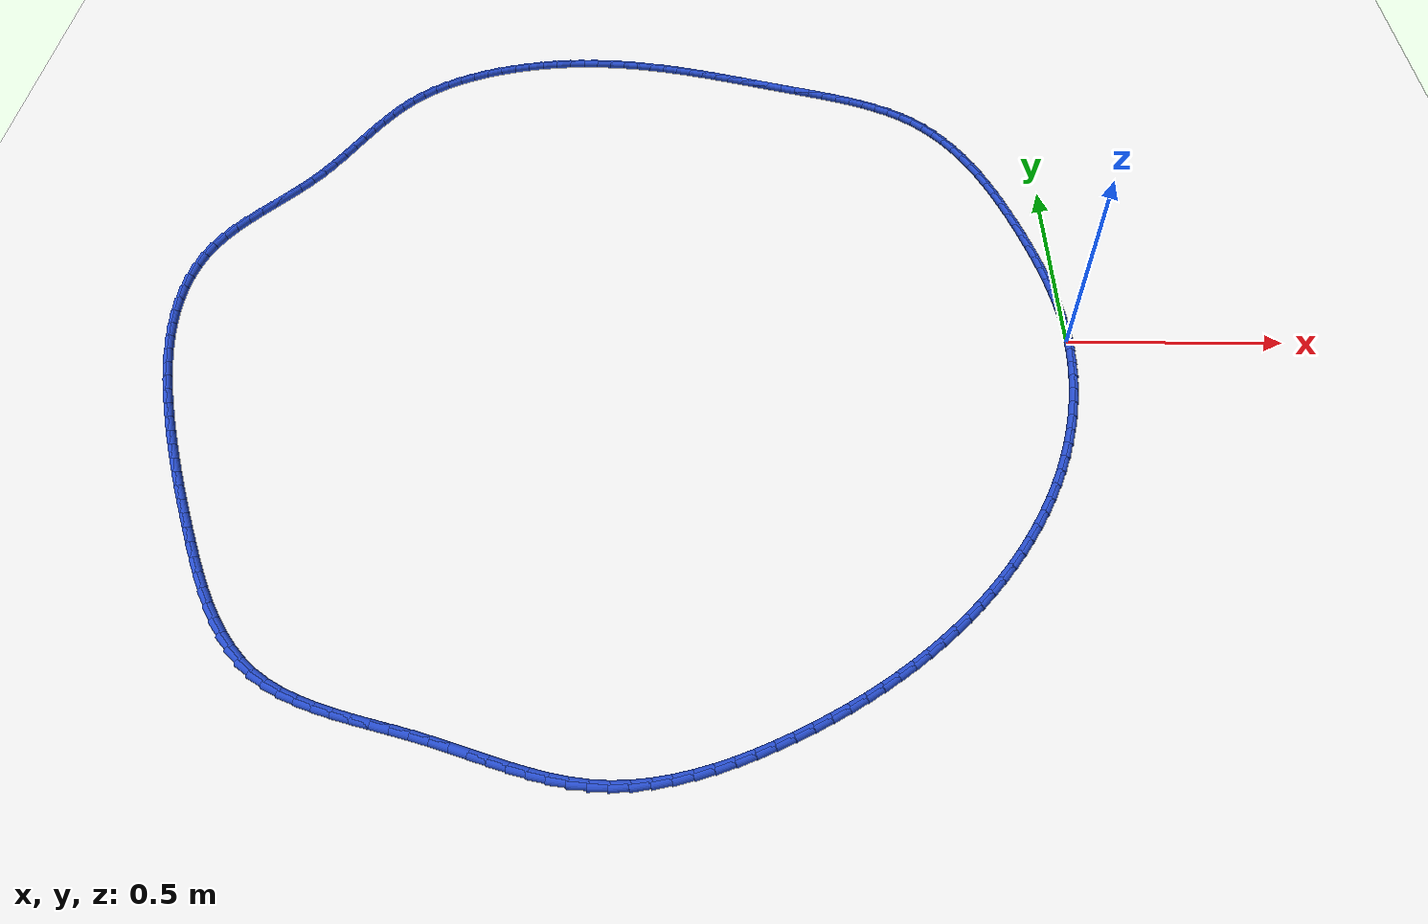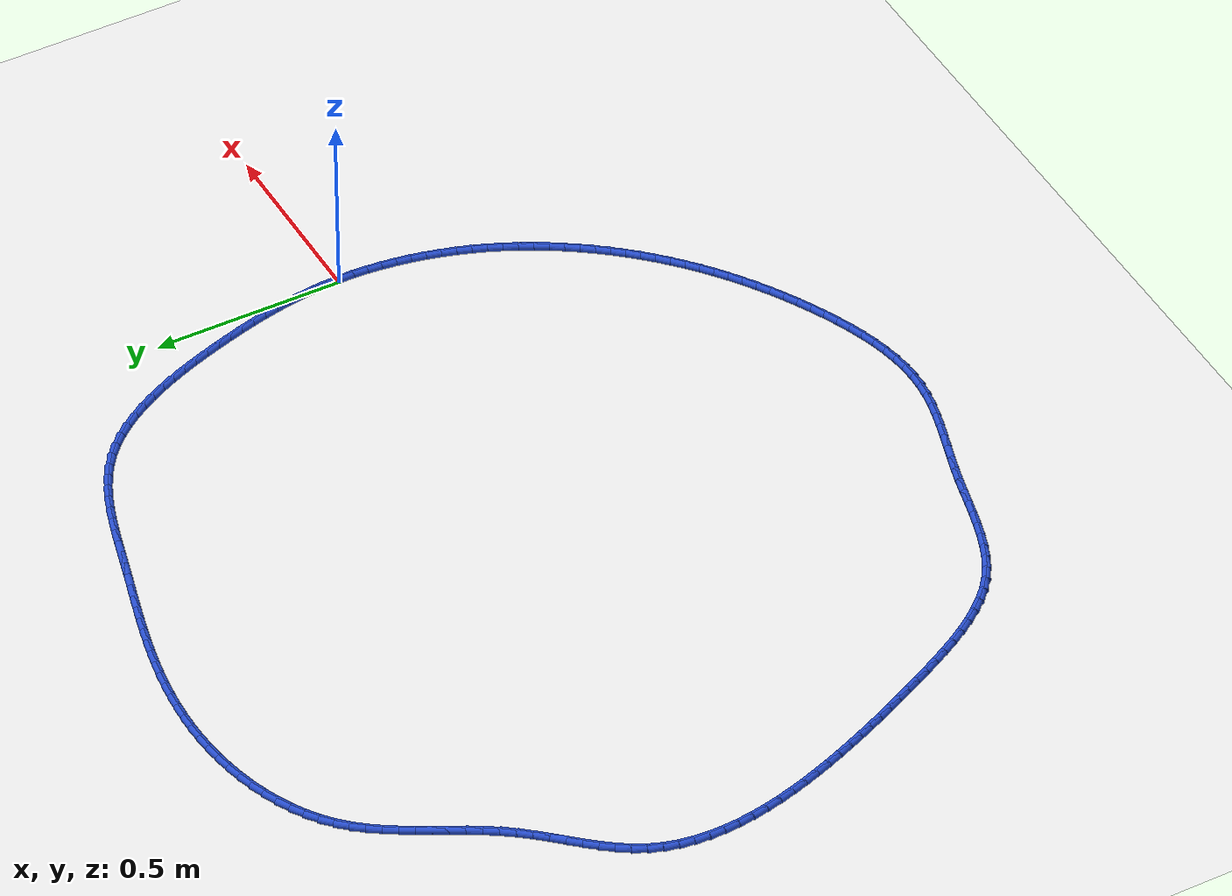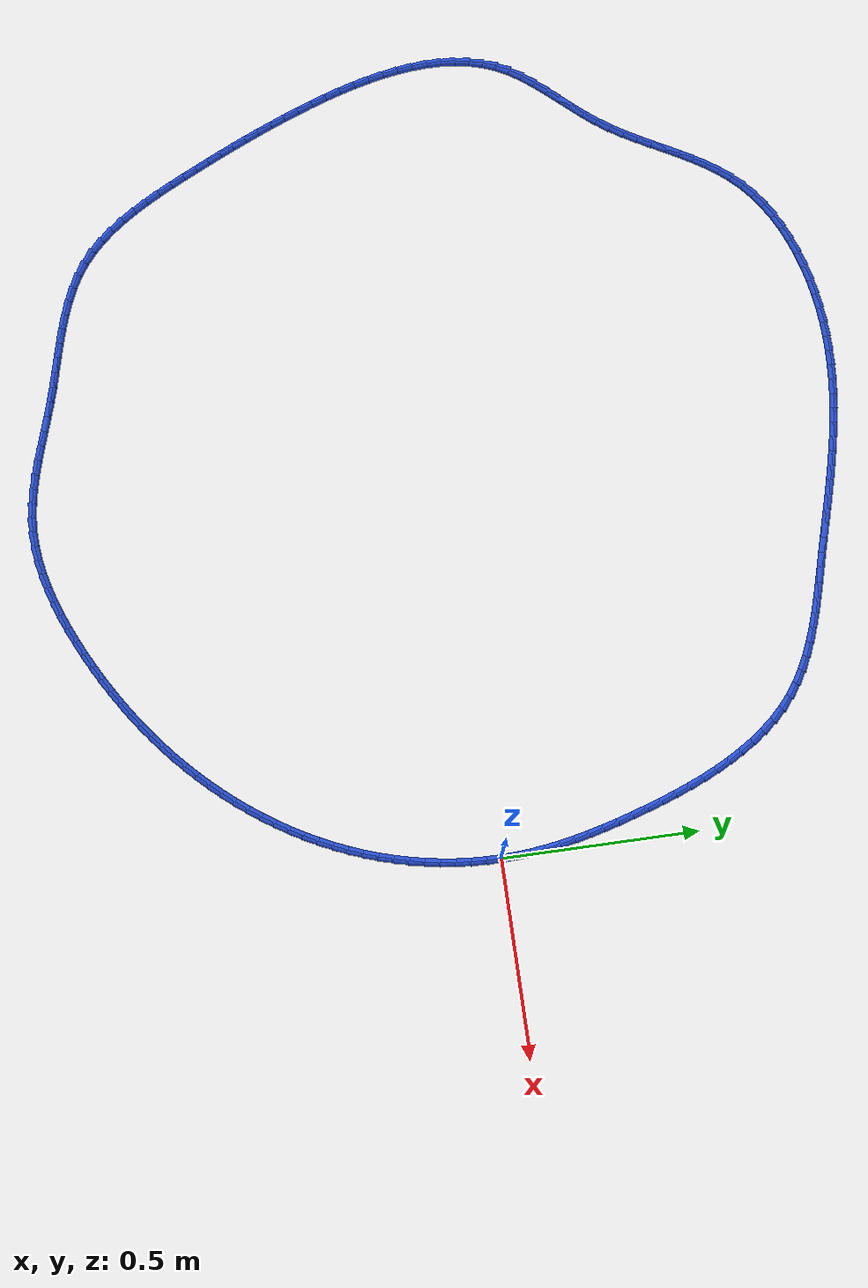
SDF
<sdf version="1.6">
 <world name="default">
  <light name="sun" type="directional">
   <pose>0 0 10 0 -0 0</pose>
   <diffuse>0.8 0.8 0.8 1</diffuse>
   <specular>0.2 0.2 0.2 1</specular>
   <attenuation>
    <range>1000</range>
    <constant>0.9</constant>
    <linear>0.01</linear>
    <quadratic>0.001</quadratic>
   </attenuation>
   <direction>-0.5 0.1 -0.9</direction>
  </light>
  <model name="ground_plane">
   <static>1</static>
   <link name="link">
    <collision name="collision">
     <geometry><plane><normal>0 0 1</normal><size>100 100</size></plane></geometry>
     <surface><friction><ode><mu>100</mu><mu2>50</mu2></ode></friction></surface>
    </collision>
    <visual name="visual">
     <cast_shadows>0</cast_shadows>
     <geometry><plane><normal>0 0 1</normal><size>100 100</size></plane></geometry>
     <material>
      <script><uri>file://media/materials/scripts/gazebo.material</uri><name>Gazebo/WhiteGlow</name></script>
     </material>
    </visual>
   </link>
  </model>
  <gravity>0 0 -9.8</gravity>
  <magnetic_field>6e-06 2.3e-05 -4.2e-05</magnetic_field>
  <atmosphere type="adiabatic"/>
  <physics name="default_physics" default="0" type="ode">
   <max_step_size>0.001</max_step_size>
   <real_time_factor>1</real_time_factor>
   <real_time_update_rate>1000</real_time_update_rate>
  </physics>
  <scene><ambient>0.4 0.4 0.4 1</ambient><background>0.7 0.7 0.7 1</background><shadows>1</shadows></scene>
  <spherical_coordinates>
   <surface_model>EARTH_WGS84</surface_model>
   <latitude_deg>0</latitude_deg>
   <longitude_deg>0</longitude_deg>
   <elevation>0</elevation>
   <heading_deg>0</heading_deg>
  </spherical_coordinates>
  <model name="line">
   <link name="link_0">
    <pose>4.5102810375396984e-17 1.1102230246251565e-16 0.01 0 1.57 -1.5336546958635322</pose>
    <collision name="collision">
     <geometry><cylinder><radius>0.01</radius><length>0.08</length></cylinder></geometry>
    </collision>
    <visual name="visual">
     <material>
      <script><name>Gazebo/Blue</name><uri>file://media/materials/scripts/gazebo.material</uri></script>
     </material>
     <geometry><cylinder><radius>0.01</radius><length>0.08</length></cylinder></geometry>
    </visual>
   </link>
   <link name="link_1">
    <pose>-0.00140859651193151 0.03790756348250111 0.01 0 1.57 -1.491874024051306</pose>
    <collision name="collision">
     <geometry><cylinder><radius>0.01</radius><length>0.08</length></cylinder></geometry>
    </collision>
    <visual name="visual">
     <material>
      <script><name>Gazebo/Blue</name><uri>file://media/materials/scripts/gazebo.material</uri></script>
     </material>
     <geometry><cylinder><radius>0.01</radius><length>0.08</length></cylinder></geometry>
    </visual>
   </link>
   <link name="link_2">
    <pose>-0.004393703759648274 0.07565236767735652 0.01 0 1.57 -1.4528920092879853</pose>
    <collision name="collision">
     <geometry><cylinder><radius>0.01</radius><length>0.08</length></cylinder></geometry>
    </collision>
    <visual name="visual">
     <material>
      <script><name>Gazebo/Blue</name><uri>file://media/materials/scripts/gazebo.material</uri></script>
     </material>
     <geometry><cylinder><radius>0.01</radius><length>0.08</length></cylinder></geometry>
    </visual>
   </link>
   <link name="link_3">
    <pose>-0.008850377984110785 0.11327612713953274 0.01 0 1.57 -1.416918304851706</pose>
    <collision name="collision">
     <geometry><cylinder><radius>0.01</radius><length>0.08</length></cylinder></geometry>
    </collision>
    <visual name="visual">
     <material>
      <script><name>Gazebo/Blue</name><uri>file://media/materials/scripts/gazebo.material</uri></script>
     </material>
     <geometry><cylinder><radius>0.01</radius><length>0.08</length></cylinder></geometry>
    </visual>
   </link>
   <link name="link_4">
    <pose>-0.014673675426279589 0.15082055642399628 0.01 0 1.57 -1.3840978174065186</pose>
    <collision name="collision">
     <geometry><cylinder><radius>0.01</radius><length>0.08</length></cylinder></geometry>
    </collision>
    <visual name="visual">
     <material>
      <script><name>Gazebo/Blue</name><uri>file://media/materials/scripts/gazebo.material</uri></script>
     </material>
     <geometry><cylinder><radius>0.01</radius><length>0.08</length></cylinder></geometry>
    </visual>
   </link>
   <link name="link_5">
    <pose>-0.021758652327115203 0.18832737008571335 0.01 0 1.57 -1.3545178188295541</pose>
    <collision name="collision">
     <geometry><cylinder><radius>0.01</radius><length>0.08</length></cylinder></geometry>
    </collision>
    <visual name="visual">
     <material>
      <script><name>Gazebo/Blue</name><uri>file://media/materials/scripts/gazebo.material</uri></script>
     </material>
     <geometry><cylinder><radius>0.01</radius><length>0.08</length></cylinder></geometry>
    </visual>
   </link>
   <link name="link_6">
    <pose>-0.030000364927578172 0.22583828267965056 0.01 0 1.57 -1.3282167747622589</pose>
    <collision name="collision">
     <geometry><cylinder><radius>0.01</radius><length>0.08</length></cylinder></geometry>
    </collision>
    <visual name="visual">
     <material>
      <script><name>Gazebo/Blue</name><uri>file://media/materials/scripts/gazebo.material</uri></script>
     </material>
     <geometry><cylinder><radius>0.01</radius><length>0.08</length></cylinder></geometry>
    </visual>
   </link>
   <link name="link_7">
    <pose>-0.039293869468629034 0.26339500876077415 0.01 0 1.57 -1.3051937319607798</pose>
    <collision name="collision">
     <geometry><cylinder><radius>0.01</radius><length>0.08</length></cylinder></geometry>
    </collision>
    <visual name="visual">
     <material>
      <script><name>Gazebo/Blue</name><uri>file://media/materials/scripts/gazebo.material</uri></script>
     </material>
     <geometry><cylinder><radius>0.01</radius><length>0.08</length></cylinder></geometry>
    </visual>
   </link>
   <link name="link_8">
    <pose>-0.049534222191228314 0.30103926288405064 0.01 0 1.57 -1.285417388623524</pose>
    <collision name="collision">
     <geometry><cylinder><radius>0.01</radius><length>0.08</length></cylinder></geometry>
    </collision>
    <visual name="visual">
     <material>
      <script><name>Gazebo/Blue</name><uri>file://media/materials/scripts/gazebo.material</uri></script>
     </material>
     <geometry><cylinder><radius>0.01</radius><length>0.08</length></cylinder></geometry>
    </visual>
   </link>
   <link name="link_9">
    <pose>-0.060616479336336564 0.3388127596044465 0.01 0 1.57 -1.2687526856826317</pose>
    <collision name="collision">
     <geometry><cylinder><radius>0.01</radius><length>0.08</length></cylinder></geometry>
    </collision>
    <visual name="visual">
     <material>
      <script><name>Gazebo/Blue</name><uri>file://media/materials/scripts/gazebo.material</uri></script>
     </material>
     <geometry><cylinder><radius>0.01</radius><length>0.08</length></cylinder></geometry>
    </visual>
   </link>
   <link name="link_10">
    <pose>-0.07243815435386722 0.37675419999924725 0.01 0 1.57 -1.2521061961875937</pose>
    <collision name="collision">
     <geometry><cylinder><radius>0.01</radius><length>0.08</length></cylinder></geometry>
    </collision>
    <visual name="visual">
     <material>
      <script><name>Gazebo/Blue</name><uri>file://media/materials/scripts/gazebo.material</uri></script>
     </material>
     <geometry><cylinder><radius>0.01</radius><length>0.08</length></cylinder></geometry>
    </visual>
   </link>
   <link name="link_11">
    <pose>-0.08498776868880197 0.41479067454722834 0.01 0 1.57 -1.2315184554474672</pose>
    <collision name="collision">
     <geometry><cylinder><radius>0.01</radius><length>0.08</length></cylinder></geometry>
    </collision>
    <visual name="visual">
     <material>
      <script><name>Gazebo/Blue</name><uri>file://media/materials/scripts/gazebo.material</uri></script>
     </material>
     <geometry><cylinder><radius>0.01</radius><length>0.08</length></cylinder></geometry>
    </visual>
   </link>
   <link name="link_12">
    <pose>-0.09836951820511933 0.4527074126618063 0.01 0 1.57 -1.2065381680521998</pose>
    <collision name="collision">
     <geometry><cylinder><radius>0.01</radius><length>0.08</length></cylinder></geometry>
    </collision>
    <visual name="visual">
     <material>
      <script><name>Gazebo/Blue</name><uri>file://media/materials/scripts/gazebo.material</uri></script>
     </material>
     <geometry><cylinder><radius>0.01</radius><length>0.08</length></cylinder></geometry>
    </visual>
   </link>
   <link name="link_13">
    <pose>-0.11269507838357525 0.49028047088642485 0.01 0 1.57 -1.1768778447251382</pose>
    <collision name="collision">
     <geometry><cylinder><radius>0.01</radius><length>0.08</length></cylinder></geometry>
    </collision>
    <visual name="visual">
     <material>
      <script><name>Gazebo/Blue</name><uri>file://media/materials/scripts/gazebo.material</uri></script>
     </material>
     <geometry><cylinder><radius>0.01</radius><length>0.08</length></cylinder></geometry>
    </visual>
   </link>
   <link name="link_14">
    <pose>-0.1280761247049258 0.5272859057645286 0.01 0 1.57 -1.1421714141123296</pose>
    <collision name="collision">
     <geometry><cylinder><radius>0.01</radius><length>0.08</length></cylinder></geometry>
    </collision>
    <visual name="visual">
     <material>
      <script><name>Gazebo/Blue</name><uri>file://media/materials/scripts/gazebo.material</uri></script>
     </material>
     <geometry><cylinder><radius>0.01</radius><length>0.08</length></cylinder></geometry>
    </visual>
   </link>
   <link name="link_15">
    <pose>-0.144624332649927 0.5634997738395618 0.01 0 1.57 -1.1019831226483308</pose>
    <collision name="collision">
     <geometry><cylinder><radius>0.01</radius><length>0.08</length></cylinder></geometry>
    </collision>
    <visual name="visual">
     <material>
      <script><name>Gazebo/Blue</name><uri>file://media/materials/scripts/gazebo.material</uri></script>
     </material>
     <geometry><cylinder><radius>0.01</radius><length>0.08</length></cylinder></geometry>
    </visual>
   </link>
   <link name="link_16">
    <pose>-0.162451377699335 0.5986981316549687 0.01 0 1.57 -1.0558230609695325</pose>
    <collision name="collision">
     <geometry><cylinder><radius>0.01</radius><length>0.08</length></cylinder></geometry>
    </collision>
    <visual name="visual">
     <material>
      <script><name>Gazebo/Blue</name><uri>file://media/materials/scripts/gazebo.material</uri></script>
     </material>
     <geometry><cylinder><radius>0.01</radius><length>0.08</length></cylinder></geometry>
    </visual>
   </link>
   <link name="link_17">
    <pose>-0.18166893533390566 0.6326570357541934 0.01 0 1.57 -1.0031742453822057</pose>
    <collision name="collision">
     <geometry><cylinder><radius>0.01</radius><length>0.08</length></cylinder></geometry>
    </collision>
    <visual name="visual">
     <material>
      <script><name>Gazebo/Blue</name><uri>file://media/materials/scripts/gazebo.material</uri></script>
     </material>
     <geometry><cylinder><radius>0.01</radius><length>0.08</length></cylinder></geometry>
    </visual>
   </link>
   <link name="link_18">
    <pose>-0.2023886810343951 0.6651525426806802 0.01 0 1.57 -0.943537311469686</pose>
    <collision name="collision">
     <geometry><cylinder><radius>0.01</radius><length>0.08</length></cylinder></geometry>
    </collision>
    <visual name="visual">
     <material>
      <script><name>Gazebo/Blue</name><uri>file://media/materials/scripts/gazebo.material</uri></script>
     </material>
     <geometry><cylinder><radius>0.01</radius><length>0.08</length></cylinder></geometry>
    </visual>
   </link>
   <link name="link_19">
    <pose>-0.22472229028155938 0.6959607089778733 0.01 0 1.57 -0.8764990840651424</pose>
    <collision name="collision">
     <geometry><cylinder><radius>0.01</radius><length>0.08</length></cylinder></geometry>
    </collision>
    <visual name="visual">
     <material>
      <script><name>Gazebo/Blue</name><uri>file://media/materials/scripts/gazebo.material</uri></script>
     </material>
     <geometry><cylinder><radius>0.01</radius><length>0.08</length></cylinder></geometry>
    </visual>
   </link>
   <link name="link_20">
    <pose>-0.2487814385561546 0.7248575911892173 0.01 0 1.57 -0.8018289759981949</pose>
    <collision name="collision">
     <geometry><cylinder><radius>0.01</radius><length>0.08</length></cylinder></geometry>
    </collision>
    <visual name="visual">
     <material>
      <script><name>Gazebo/Blue</name><uri>file://media/materials/scripts/gazebo.material</uri></script>
     </material>
     <geometry><cylinder><radius>0.01</radius><length>0.08</length></cylinder></geometry>
    </visual>
   </link>
   <link name="link_21">
    <pose>-0.27467780133893666 0.7516192458581561 0.01 0 1.57 -0.7196001107904848</pose>
    <collision name="collision">
     <geometry><cylinder><radius>0.01</radius><length>0.08</length></cylinder></geometry>
    </collision>
    <visual name="visual">
     <material>
      <script><name>Gazebo/Blue</name><uri>file://media/materials/scripts/gazebo.material</uri></script>
     </material>
     <geometry><cylinder><radius>0.01</radius><length>0.08</length></cylinder></geometry>
    </visual>
   </link>
   <link name="link_22">
    <pose>-0.3025230541106615 0.776021729528134 0.01 0 1.57 -0.6312192984566917</pose>
    <collision name="collision">
     <geometry><cylinder><radius>0.01</radius><length>0.08</length></cylinder></geometry>
    </collision>
    <visual name="visual">
     <material>
      <script><name>Gazebo/Blue</name><uri>file://media/materials/scripts/gazebo.material</uri></script>
     </material>
     <geometry><cylinder><radius>0.01</radius><length>0.08</length></cylinder></geometry>
    </visual>
   </link>
   <link name="link_23">
    <pose>-0.33240955889382645 0.7978682827386274 0.01 0 1.57 -0.5476141615328594</pose>
    <collision name="collision">
     <geometry><cylinder><radius>0.01</radius><length>0.08</length></cylinder></geometry>
    </collision>
    <visual name="visual">
     <material>
      <script><name>Gazebo/Blue</name><uri>file://media/materials/scripts/gazebo.material</uri></script>
     </material>
     <geometry><cylinder><radius>0.01</radius><length>0.08</length></cylinder></geometry>
    </visual>
   </link>
   <link name="link_24">
    <pose>-0.36421509828093884 0.8172641699491763 0.01 0 1.57 -0.4756373567214833</pose>
    <collision name="collision">
     <geometry><cylinder><radius>0.01</radius><length>0.08</length></cylinder></geometry>
    </collision>
    <visual name="visual">
     <material>
      <script><name>Gazebo/Blue</name><uri>file://media/materials/scripts/gazebo.material</uri></script>
     </material>
     <geometry><cylinder><radius>0.01</radius><length>0.08</length></cylinder></geometry>
    </visual>
   </link>
   <link name="link_25">
    <pose>-0.3976835945579607 0.8345030661045459 0.01 0 1.57 -0.41532754965614477</pose>
    <collision name="collision">
     <geometry><cylinder><radius>0.01</radius><length>0.08</length></cylinder></geometry>
    </collision>
    <visual name="visual">
     <material>
      <script><name>Gazebo/Blue</name><uri>file://media/materials/scripts/gazebo.material</uri></script>
     </material>
     <geometry><cylinder><radius>0.01</radius><length>0.08</length></cylinder></geometry>
    </visual>
   </link>
   <link name="link_26">
    <pose>-0.4325569359528952 0.8498815091180465 0.01 0 1.57 -0.36622188825695445</pose>
    <collision name="collision">
     <geometry><cylinder><radius>0.01</radius><length>0.08</length></cylinder></geometry>
    </collision>
    <visual name="visual">
     <material>
      <script><name>Gazebo/Blue</name><uri>file://media/materials/scripts/gazebo.material</uri></script>
     </material>
     <geometry><cylinder><radius>0.01</radius><length>0.08</length></cylinder></geometry>
    </visual>
   </link>
   <link name="link_27">
    <pose>-0.468577010693745 0.8636960369029889 0.01 0 1.57 -0.327694638188425</pose>
    <collision name="collision">
     <geometry><cylinder><radius>0.01</radius><length>0.08</length></cylinder></geometry>
    </collision>
    <visual name="visual">
     <material>
      <script><name>Gazebo/Blue</name><uri>file://media/materials/scripts/gazebo.material</uri></script>
     </material>
     <geometry><cylinder><radius>0.01</radius><length>0.08</length></cylinder></geometry>
    </visual>
   </link>
   <link name="link_28">
    <pose>-0.5054857070085138 0.8762431873726835 0.01 0 1.57 -0.29912631322043587</pose>
    <collision name="collision">
     <geometry><cylinder><radius>0.01</radius><length>0.08</length></cylinder></geometry>
    </collision>
    <visual name="visual">
     <material>
      <script><name>Gazebo/Blue</name><uri>file://media/materials/scripts/gazebo.material</uri></script>
     </material>
     <geometry><cylinder><radius>0.01</radius><length>0.08</length></cylinder></geometry>
    </visual>
   </link>
   <link name="link_29">
    <pose>-0.5430249131252038 0.8878194984404401 0.01 0 1.57 -0.28000886338028597</pose>
    <collision name="collision">
     <geometry><cylinder><radius>0.01</radius><length>0.08</length></cylinder></geometry>
    </collision>
    <visual name="visual">
     <material>
      <script><name>Gazebo/Blue</name><uri>file://media/materials/scripts/gazebo.material</uri></script>
     </material>
     <geometry><cylinder><radius>0.01</radius><length>0.08</length></cylinder></geometry>
    </visual>
   </link>
   <link name="link_30">
    <pose>-0.5809365172718185 0.8987215080195696 0.01 0 1.57 -0.2700066309234214</pose>
    <collision name="collision">
     <geometry><cylinder><radius>0.01</radius><length>0.08</length></cylinder></geometry>
    </collision>
    <visual name="visual">
     <material>
      <script><name>Gazebo/Blue</name><uri>file://media/materials/scripts/gazebo.material</uri></script>
     </material>
     <geometry><cylinder><radius>0.01</radius><length>0.08</length></cylinder></geometry>
    </visual>
   </link>
   <link name="link_31">
    <pose>-0.6189624076763609 0.9092457540233827 0.01 0 1.57 -0.26898590548891355</pose>
    <collision name="collision">
     <geometry><cylinder><radius>0.01</radius><length>0.08</length></cylinder></geometry>
    </collision>
    <visual name="visual">
     <material>
      <script><name>Gazebo/Blue</name><uri>file://media/materials/scripts/gazebo.material</uri></script>
     </material>
     <geometry><cylinder><radius>0.01</radius><length>0.08</length></cylinder></geometry>
    </visual>
   </link>
   <link name="link_32">
    <pose>-0.6568445999169088 0.9196886119122679 0.01 0 1.57 -0.27399904156337</pose>
    <collision name="collision">
     <geometry><cylinder><radius>0.01</radius><length>0.08</length></cylinder></geometry>
    </collision>
    <visual name="visual">
     <material>
      <script><name>Gazebo/Blue</name><uri>file://media/materials/scripts/gazebo.material</uri></script>
     </material>
     <geometry><cylinder><radius>0.01</radius><length>0.08</length></cylinder></geometry>
    </visual>
   </link>
   <link name="link_33">
    <pose>-0.6944042913295657 0.9302454496844453 0.01 0 1.57 -0.27690350027894656</pose>
    <collision name="collision">
     <geometry><cylinder><radius>0.01</radius><length>0.08</length></cylinder></geometry>
    </collision>
    <visual name="visual">
     <material>
      <script><name>Gazebo/Blue</name><uri>file://media/materials/scripts/gazebo.material</uri></script>
     </material>
     <geometry><cylinder><radius>0.01</radius><length>0.08</length></cylinder></geometry>
    </visual>
   </link>
   <link name="link_34">
    <pose>-0.731676813019081 0.9408384776175218 0.01 0 1.57 -0.27625584032233397</pose>
    <collision name="collision">
     <geometry><cylinder><radius>0.01</radius><length>0.08</length></cylinder></geometry>
    </collision>
    <visual name="visual">
     <material>
      <script><name>Gazebo/Blue</name><uri>file://media/materials/scripts/gazebo.material</uri></script>
     </material>
     <geometry><cylinder><radius>0.01</radius><length>0.08</length></cylinder></geometry>
    </visual>
   </link>
   <link name="link_35">
    <pose>-0.7687333380848786 0.9513441844869389 0.01 0 1.57 -0.27199343530642894</pose>
    <collision name="collision">
     <geometry><cylinder><radius>0.01</radius><length>0.08</length></cylinder></geometry>
    </collision>
    <visual name="visual">
     <material>
      <script><name>Gazebo/Blue</name><uri>file://media/materials/scripts/gazebo.material</uri></script>
     </material>
     <geometry><cylinder><radius>0.01</radius><length>0.08</length></cylinder></geometry>
    </visual>
   </link>
   <link name="link_36">
    <pose>-0.8056450396263832 0.9616390590681381 0.01 0 1.57 -0.2640725277609289</pose>
    <collision name="collision">
     <geometry><cylinder><radius>0.01</radius><length>0.08</length></cylinder></geometry>
    </collision>
    <visual name="visual">
     <material>
      <script><name>Gazebo/Blue</name><uri>file://media/materials/scripts/gazebo.material</uri></script>
     </material>
     <geometry><cylinder><radius>0.01</radius><length>0.08</length></cylinder></geometry>
    </visual>
   </link>
   <link name="link_37">
    <pose>-0.8424830907430182 0.9715995901365594 0.01 0 1.57 -0.25247083539170967</pose>
    <collision name="collision">
     <geometry><cylinder><radius>0.01</radius><length>0.08</length></cylinder></geometry>
    </collision>
    <visual name="visual">
     <material>
      <script><name>Gazebo/Blue</name><uri>file://media/materials/scripts/gazebo.material</uri></script>
     </material>
     <geometry><cylinder><radius>0.01</radius><length>0.08</length></cylinder></geometry>
    </visual>
   </link>
   <link name="link_38">
    <pose>-0.8793186645342077 0.9811022664676445 0.01 0 1.57 -0.23719141389137738</pose>
    <collision name="collision">
     <geometry><cylinder><radius>0.01</radius><length>0.08</length></cylinder></geometry>
    </collision>
    <visual name="visual">
     <material>
      <script><name>Gazebo/Blue</name><uri>file://media/materials/scripts/gazebo.material</uri></script>
     </material>
     <geometry><cylinder><radius>0.01</radius><length>0.08</length></cylinder></geometry>
    </visual>
   </link>
   <link name="link_39">
    <pose>-0.9162229340993756 0.9900235768368337 0.01 0 1.57 -0.2182676704546696</pose>
    <collision name="collision">
     <geometry><cylinder><radius>0.01</radius><length>0.08</length></cylinder></geometry>
    </collision>
    <visual name="visual">
     <material>
      <script><name>Gazebo/Blue</name><uri>file://media/materials/scripts/gazebo.material</uri></script>
     </material>
     <geometry><cylinder><radius>0.01</radius><length>0.08</length></cylinder></geometry>
    </visual>
   </link>
   <link name="link_40">
    <pose>-0.9532670725379462 0.9982400100195686 0.01 0 1.57 -0.19577565909470604</pose>
    <collision name="collision">
     <geometry><cylinder><radius>0.01</radius><length>0.08</length></cylinder></geometry>
    </collision>
    <visual name="visual">
     <material>
      <script><name>Gazebo/Blue</name><uri>file://media/materials/scripts/gazebo.material</uri></script>
     </material>
     <geometry><cylinder><radius>0.01</radius><length>0.08</length></cylinder></geometry>
    </visual>
   </link>
   <link name="link_41">
    <pose>-0.9905215291467588 1.0056281591503855 0.01 0 1.57 -0.17009278077393494</pose>
    <collision name="collision">
     <geometry><cylinder><radius>0.01</radius><length>0.08</length></cylinder></geometry>
    </collision>
    <visual name="visual">
     <material>
      <script><name>Gazebo/Blue</name><uri>file://media/materials/scripts/gazebo.material</uri></script>
     </material>
     <geometry><cylinder><radius>0.01</radius><length>0.08</length></cylinder></geometry>
    </visual>
   </link>
   <link name="link_42">
    <pose>-1.0280241378965373 1.01206931989738 0.01 0 1.57 -0.14163893846656542</pose>
    <collision name="collision">
     <geometry><cylinder><radius>0.01</radius><length>0.08</length></cylinder></geometry>
    </collision>
    <visual name="visual">
     <material>
      <script><name>Gazebo/Blue</name><uri>file://media/materials/scripts/gazebo.material</uri></script>
     </material>
     <geometry><cylinder><radius>0.01</radius><length>0.08</length></cylinder></geometry>
    </visual>
   </link>
   <link name="link_43">
    <pose>-1.0657675750418658 1.0174512988454736 0.01 0 1.57 -0.11044365113428964</pose>
    <collision name="collision">
     <geometry><cylinder><radius>0.01</radius><length>0.08</length></cylinder></geometry>
    </collision>
    <visual name="visual">
     <material>
      <script><name>Gazebo/Blue</name><uri>file://media/materials/scripts/gazebo.material</uri></script>
     </material>
     <geometry><cylinder><radius>0.01</radius><length>0.08</length></cylinder></geometry>
    </visual>
   </link>
   <link name="link_44">
    <pose>-1.1037412010078642 1.021662380661557 0.01 0 1.57 -0.07652546785735674</pose>
    <collision name="collision">
     <geometry><cylinder><radius>0.01</radius><length>0.08</length></cylinder></geometry>
    </collision>
    <visual name="visual">
     <material>
      <script><name>Gazebo/Blue</name><uri>file://media/materials/scripts/gazebo.material</uri></script>
     </material>
     <geometry><cylinder><radius>0.01</radius><length>0.08</length></cylinder></geometry>
    </visual>
   </link>
   <link name="link_45">
    <pose>-1.141934376219652 1.0245908500125198 0.01 0 1.57 -0.039928201726243895</pose>
    <collision name="collision">
     <geometry><cylinder><radius>0.01</radius><length>0.08</length></cylinder></geometry>
    </collision>
    <visual name="visual">
     <material>
      <script><name>Gazebo/Blue</name><uri>file://media/materials/scripts/gazebo.material</uri></script>
     </material>
     <geometry><cylinder><radius>0.01</radius><length>0.08</length></cylinder></geometry>
    </visual>
   </link>
   <link name="link_46">
    <pose>-1.1803364611023484 1.0261249915652535 0.01 0 1.57 -0.0007279315552040474</pose>
    <collision name="collision">
     <geometry><cylinder><radius>0.01</radius><length>0.08</length></cylinder></geometry>
    </collision>
    <visual name="visual">
     <material>
      <script><name>Gazebo/Blue</name><uri>file://media/materials/scripts/gazebo.material</uri></script>
     </material>
     <geometry><cylinder><radius>0.01</radius><length>0.08</length></cylinder></geometry>
    </visual>
   </link>
   <link name="link_47">
    <pose>-1.218936816081073 1.0261530899866476 0.01 0 1.57 0.04096038770682659</pose>
    <collision name="collision">
     <geometry><cylinder><radius>0.01</radius><length>0.08</length></cylinder></geometry>
    </collision>
    <visual name="visual">
     <material>
      <script><name>Gazebo/Blue</name><uri>file://media/materials/scripts/gazebo.material</uri></script>
     </material>
     <geometry><cylinder><radius>0.01</radius><length>0.08</length></cylinder></geometry>
    </visual>
   </link>
   <link name="link_48">
    <pose>-1.2577248015809452 1.024563429943593 0.01 0 1.57 0.08497735586148884</pose>
    <collision name="collision">
     <geometry><cylinder><radius>0.01</radius><length>0.08</length></cylinder></geometry>
    </collision>
    <visual name="visual">
     <material>
      <script><name>Gazebo/Blue</name><uri>file://media/materials/scripts/gazebo.material</uri></script>
     </material>
     <geometry><cylinder><radius>0.01</radius><length>0.08</length></cylinder></geometry>
    </visual>
   </link>
   <link name="link_49">
    <pose>-1.2966897780270845 1.0212442961029802 0.01 0 1.57 0.13109465278531335</pose>
    <collision name="collision">
     <geometry><cylinder><radius>0.01</radius><length>0.08</length></cylinder></geometry>
    </collision>
    <visual name="visual">
     <material>
      <script><name>Gazebo/Blue</name><uri>file://media/materials/scripts/gazebo.material</uri></script>
     </material>
     <geometry><cylinder><radius>0.01</radius><length>0.08</length></cylinder></geometry>
    </visual>
   </link>
   <link name="link_50">
    <pose>-1.3358115884547324 1.0160860525096407 0.01 0 1.57 0.17895395203966896</pose>
    <collision name="collision">
     <geometry><cylinder><radius>0.01</radius><length>0.08</length></cylinder></geometry>
    </collision>
    <visual name="visual">
     <material>
      <script><name>Gazebo/Blue</name><uri>file://media/materials/scripts/gazebo.material</uri></script>
     </material>
     <geometry><cylinder><radius>0.01</radius><length>0.08</length></cylinder></geometry>
    </visual>
   </link>
   <link name="link_51">
    <pose>-1.3749222060982327 1.0090113700915038 0.01 0 1.57 0.22889449513166307</pose>
    <collision name="collision">
     <geometry><cylinder><radius>0.01</radius><length>0.08</length></cylinder></geometry>
    </collision>
    <visual name="visual">
     <material>
      <script><name>Gazebo/Blue</name><uri>file://media/materials/scripts/gazebo.material</uri></script>
     </material>
     <geometry><cylinder><radius>0.01</radius><length>0.08</length></cylinder></geometry>
    </visual>
   </link>
   <link name="link_52">
    <pose>-1.4137369141755376 0.9999684144393381 0.01 0 1.57 0.28166393329170697</pose>
    <collision name="collision">
     <geometry><cylinder><radius>0.01</radius><length>0.08</length></cylinder></geometry>
    </collision>
    <visual name="visual">
     <material>
      <script><name>Gazebo/Blue</name><uri>file://media/materials/scripts/gazebo.material</uri></script>
     </material>
     <geometry><cylinder><radius>0.01</radius><length>0.08</length></cylinder></geometry>
    </visual>
   </link>
   <link name="link_53">
    <pose>-1.4519678243027645 0.9889060440816805 0.01 0 1.57 0.33803811700745473</pose>
    <collision name="collision">
     <geometry><cylinder><radius>0.01</radius><length>0.08</length></cylinder></geometry>
    </collision>
    <visual name="visual">
     <material>
      <script><name>Gazebo/Blue</name><uri>file://media/materials/scripts/gazebo.material</uri></script>
     </material>
     <geometry><cylinder><radius>0.01</radius><length>0.08</length></cylinder></geometry>
    </visual>
   </link>
   <link name="link_54">
    <pose>-1.4893270480960323 0.9757731175470671 0.01 0 1.57 0.39881962750737726</pose>
    <collision name="collision">
     <geometry><cylinder><radius>0.01</radius><length>0.08</length></cylinder></geometry>
    </collision>
    <visual name="visual">
     <material>
      <script><name>Gazebo/Blue</name><uri>file://media/materials/scripts/gazebo.material</uri></script>
     </material>
     <geometry><cylinder><radius>0.01</radius><length>0.08</length></cylinder></geometry>
    </visual>
   </link>
   <link name="link_55">
    <pose>-1.5255266971714605 0.9605184933640343 0.01 0 1.57 0.4648294612416513</pose>
    <collision name="collision">
     <geometry><cylinder><radius>0.01</radius><length>0.08</length></cylinder></geometry>
    </collision>
    <visual name="visual">
     <material>
      <script><name>Gazebo/Blue</name><uri>file://media/materials/scripts/gazebo.material</uri></script>
     </material>
     <geometry><cylinder><radius>0.01</radius><length>0.08</length></cylinder></geometry>
    </visual>
   </link>
   <link name="link_56">
    <pose>-1.5602788831451664 0.943091030061118 0.01 0 1.57 0.5368786773176236</pose>
    <collision name="collision">
     <geometry><cylinder><radius>0.01</radius><length>0.08</length></cylinder></geometry>
    </collision>
    <visual name="visual">
     <material>
      <script><name>Gazebo/Blue</name><uri>file://media/materials/scripts/gazebo.material</uri></script>
     </material>
     <geometry><cylinder><radius>0.01</radius><length>0.08</length></cylinder></geometry>
    </visual>
   </link>
   <link name="link_57">
    <pose>-1.5932957176332694 0.9234395861668555 0.01 0 1.57 0.6157116546575448</pose>
    <collision name="collision">
     <geometry><cylinder><radius>0.01</radius><length>0.08</length></cylinder></geometry>
    </collision>
    <visual name="visual">
     <material>
      <script><name>Gazebo/Blue</name><uri>file://media/materials/scripts/gazebo.material</uri></script>
     </material>
     <geometry><cylinder><radius>0.01</radius><length>0.08</length></cylinder></geometry>
    </visual>
   </link>
   <link name="link_58">
    <pose>-1.624289312251888 0.9015130202097821 0.01 0 1.57 0.7019124532417944</pose>
    <collision name="collision">
     <geometry><cylinder><radius>0.01</radius><length>0.08</length></cylinder></geometry>
    </collision>
    <visual name="visual">
     <material>
      <script><name>Gazebo/Blue</name><uri>file://media/materials/scripts/gazebo.material</uri></script>
     </material>
     <geometry><cylinder><radius>0.01</radius><length>0.08</length></cylinder></geometry>
    </visual>
   </link>
   <link name="link_59">
    <pose>-1.6529717786171392 0.8772601907184344 0.01 0 1.57 0.794905887057208</pose>
    <collision name="collision">
     <geometry><cylinder><radius>0.01</radius><length>0.08</length></cylinder></geometry>
    </collision>
    <visual name="visual">
     <material>
      <script><name>Gazebo/Blue</name><uri>file://media/materials/scripts/gazebo.material</uri></script>
     </material>
     <geometry><cylinder><radius>0.01</radius><length>0.08</length></cylinder></geometry>
    </visual>
   </link>
   <link name="link_60">
    <pose>-1.6790845112794848 0.8506461311801722 0.01 0 1.57 0.8820594149023839</pose>
    <collision name="collision">
     <geometry><cylinder><radius>0.01</radius><length>0.08</length></cylinder></geometry>
    </collision>
    <visual name="visual">
     <material>
      <script><name>Gazebo/Blue</name><uri>file://media/materials/scripts/gazebo.material</uri></script>
     </material>
     <geometry><cylinder><radius>0.01</radius><length>0.08</length></cylinder></geometry>
    </visual>
   </link>
   <link name="link_61">
    <pose>-1.7027794860190124 0.8218626670563252 0.01 0 1.57 0.9531725428583507</pose>
    <collision name="collision">
     <geometry><cylinder><radius>0.01</radius><length>0.08</length></cylinder></geometry>
    </collision>
    <visual name="visual">
     <material>
      <script><name>Gazebo/Blue</name><uri>file://media/materials/scripts/gazebo.material</uri></script>
     </material>
     <geometry><cylinder><radius>0.01</radius><length>0.08</length></cylinder></geometry>
    </visual>
   </link>
   <link name="link_62">
    <pose>-1.7245112083551781 0.7912687315857454 0.01 0 1.57 1.0076312658905597</pose>
    <collision name="collision">
     <geometry><cylinder><radius>0.01</radius><length>0.08</length></cylinder></geometry>
    </collision>
    <visual name="visual">
     <material>
      <script><name>Gazebo/Blue</name><uri>file://media/materials/scripts/gazebo.material</uri></script>
     </material>
     <geometry><cylinder><radius>0.01</radius><length>0.08</length></cylinder></geometry>
    </visual>
   </link>
   <link name="link_63">
    <pose>-1.7447412226518912 0.7592271460404268 0.01 0 1.57 1.0457428436793283</pose>
    <collision name="collision">
     <geometry><cylinder><radius>0.01</radius><length>0.08</length></cylinder></geometry>
    </collision>
    <visual name="visual">
     <material>
      <script><name>Gazebo/Blue</name><uri>file://media/materials/scripts/gazebo.material</uri></script>
     </material>
     <geometry><cylinder><radius>0.01</radius><length>0.08</length></cylinder></geometry>
    </visual>
   </link>
   <link name="link_64">
    <pose>-1.7639310732730613 0.7261007316923632 0.01 0 1.57 1.0680756240421299</pose>
    <collision name="collision">
     <geometry><cylinder><radius>0.01</radius><length>0.08</length></cylinder></geometry>
    </collision>
    <visual name="visual">
     <material>
      <script><name>Gazebo/Blue</name><uri>file://media/materials/scripts/gazebo.material</uri></script>
     </material>
     <geometry><cylinder><radius>0.01</radius><length>0.08</length></cylinder></geometry>
    </visual>
   </link>
   <link name="link_65">
    <pose>-1.7825423045825972 0.6922523098135481 0.01 0 1.57 1.0751641779594607</pose>
    <collision name="collision">
     <geometry><cylinder><radius>0.01</radius><length>0.08</length></cylinder></geometry>
    </collision>
    <visual name="visual">
     <material>
      <script><name>Gazebo/Blue</name><uri>file://media/materials/scripts/gazebo.material</uri></script>
     </material>
     <geometry><cylinder><radius>0.01</radius><length>0.08</length></cylinder></geometry>
    </visual>
   </link>
   <link name="link_66">
    <pose>-1.8010364609444085 0.658044701675975 0.01 0 1.57 1.0673598155734774</pose>
    <collision name="collision">
     <geometry><cylinder><radius>0.01</radius><length>0.08</length></cylinder></geometry>
    </collision>
    <visual name="visual">
     <material>
      <script><name>Gazebo/Blue</name><uri>file://media/materials/scripts/gazebo.material</uri></script>
     </material>
     <geometry><cylinder><radius>0.01</radius><length>0.08</length></cylinder></geometry>
    </visual>
   </link>
   <link name="link_67">
    <pose>-1.8198750867224043 0.6238407285516377 0.01 0 1.57 1.0447951288060568</pose>
    <collision name="collision">
     <geometry><cylinder><radius>0.01</radius><length>0.08</length></cylinder></geometry>
    </collision>
    <visual name="visual">
     <material>
      <script><name>Gazebo/Blue</name><uri>file://media/materials/scripts/gazebo.material</uri></script>
     </material>
     <geometry><cylinder><radius>0.01</radius><length>0.08</length></cylinder></geometry>
    </visual>
   </link>
   <link name="link_68">
    <pose>-1.839519726280494 0.5900032117125297 0.01 0 1.57 1.0074426961574314</pose>
    <collision name="collision">
     <geometry><cylinder><radius>0.01</radius><length>0.08</length></cylinder></geometry>
    </collision>
    <visual name="visual">
     <material>
      <script><name>Gazebo/Blue</name><uri>file://media/materials/scripts/gazebo.material</uri></script>
     </material>
     <geometry><cylinder><radius>0.01</radius><length>0.08</length></cylinder></geometry>
    </visual>
   </link>
   <link name="link_69">
    <pose>-1.860431923982586 0.5568949724306447 0.01 0 1.57 0.9552961262351105</pose>
    <collision name="collision">
     <geometry><cylinder><radius>0.01</radius><length>0.08</length></cylinder></geometry>
    </collision>
    <visual name="visual">
     <material>
      <script><name>Gazebo/Blue</name><uri>file://media/materials/scripts/gazebo.material</uri></script>
     </material>
     <geometry><cylinder><radius>0.01</radius><length>0.08</length></cylinder></geometry>
    </visual>
   </link>
   <link name="link_70">
    <pose>-1.883072185392148 0.5248781994744346 0.01 0 1.57 0.8981610780099987</pose>
    <collision name="collision">
     <geometry><cylinder><radius>0.01</radius><length>0.08</length></cylinder></geometry>
    </collision>
    <visual name="visual">
     <material>
      <script><name>Gazebo/Blue</name><uri>file://media/materials/scripts/gazebo.material</uri></script>
     </material>
     <geometry><cylinder><radius>0.01</radius><length>0.08</length></cylinder></geometry>
    </visual>
   </link>
   <link name="link_71">
    <pose>-1.9075752904595844 0.4941167541997968 0.01 0 1.57 0.8592301685371411</pose>
    <collision name="collision">
     <geometry><cylinder><radius>0.01</radius><length>0.08</length></cylinder></geometry>
    </collision>
    <visual name="visual">
     <material>
      <script><name>Gazebo/Blue</name><uri>file://media/materials/scripts/gazebo.material</uri></script>
     </material>
     <geometry><cylinder><radius>0.01</radius><length>0.08</length></cylinder></geometry>
    </visual>
   </link>
   <link name="link_72">
    <pose>-1.9332890040619934 0.4642953011881951 0.01 0 1.57 0.8414916160327705</pose>
    <collision name="collision">
     <geometry><cylinder><radius>0.01</radius><length>0.08</length></cylinder></geometry>
    </collision>
    <visual name="visual">
     <material>
      <script><name>Gazebo/Blue</name><uri>file://media/materials/scripts/gazebo.material</uri></script>
     </material>
     <geometry><cylinder><radius>0.01</radius><length>0.08</length></cylinder></geometry>
    </visual>
   </link>
   <link name="link_73">
    <pose>-1.959444587094193 0.4350275682189757 0.01 0 1.57 0.8448878969377035</pose>
    <collision name="collision">
     <geometry><cylinder><radius>0.01</radius><length>0.08</length></cylinder></geometry>
    </collision>
    <visual name="visual">
     <material>
      <script><name>Gazebo/Blue</name><uri>file://media/materials/scripts/gazebo.material</uri></script>
     </material>
     <geometry><cylinder><radius>0.01</radius><length>0.08</length></cylinder></geometry>
    </visual>
   </link>
   <link name="link_74">
    <pose>-1.9852733004509997 0.4059272830714846 0.01 0 1.57 0.8700394349712718</pose>
    <collision name="collision">
     <geometry><cylinder><radius>0.01</radius><length>0.08</length></cylinder></geometry>
    </collision>
    <visual name="visual">
     <material>
      <script><name>Gazebo/Blue</name><uri>file://media/materials/scripts/gazebo.material</uri></script>
     </material>
     <geometry><cylinder><radius>0.01</radius><length>0.08</length></cylinder></geometry>
    </visual>
   </link>
   <link name="link_75">
    <pose>-2.01000640502723 0.3766081735250689 0.01 0 1.57 0.918254676814643</pose>
    <collision name="collision">
     <geometry><cylinder><radius>0.01</radius><length>0.08</length></cylinder></geometry>
    </collision>
    <visual name="visual">
     <material>
      <script><name>Gazebo/Blue</name><uri>file://media/materials/scripts/gazebo.material</uri></script>
     </material>
     <geometry><cylinder><radius>0.01</radius><length>0.08</length></cylinder></geometry>
    </visual>
   </link>
   <link name="link_76">
    <pose>-2.0328751617177017 0.34668396735907475 0.01 0 1.57 0.9912318749209386</pose>
    <collision name="collision">
     <geometry><cylinder><radius>0.01</radius><length>0.08</length></cylinder></geometry>
    </collision>
    <visual name="visual">
     <material>
      <script><name>Gazebo/Blue</name><uri>file://media/materials/scripts/gazebo.material</uri></script>
     </material>
     <geometry><cylinder><radius>0.01</radius><length>0.08</length></cylinder></geometry>
    </visual>
   </link>
   <link name="link_77">
    <pose>-2.0531108314172326 0.31576839235284837 0.01 0 1.57 1.089987411629745</pose>
    <collision name="collision">
     <geometry><cylinder><radius>0.01</radius><length>0.08</length></cylinder></geometry>
    </collision>
    <visual name="visual">
     <material>
      <script><name>Gazebo/Blue</name><uri>file://media/materials/scripts/gazebo.material</uri></script>
     </material>
     <geometry><cylinder><radius>0.01</radius><length>0.08</length></cylinder></geometry>
    </visual>
   </link>
   <link name="link_78">
    <pose>-2.069953657429364 0.28348013959036855 0.01 0 1.57 1.201400040271018</pose>
    <collision name="collision">
     <geometry><cylinder><radius>0.01</radius><length>0.08</length></cylinder></geometry>
    </collision>
    <visual name="visual">
     <material>
      <script><name>Gazebo/Blue</name><uri>file://media/materials/scripts/gazebo.material</uri></script>
     </material>
     <geometry><cylinder><radius>0.01</radius><length>0.08</length></cylinder></geometry>
    </visual>
   </link>
   <link name="link_79">
    <pose>-2.083047420044782 0.24966087787332933 0.01 0 1.57 1.3059615899931232</pose>
    <collision name="collision">
     <geometry><cylinder><radius>0.01</radius><length>0.08</length></cylinder></geometry>
    </collision>
    <visual name="visual">
     <material>
      <script><name>Gazebo/Blue</name><uri>file://media/materials/scripts/gazebo.material</uri></script>
     </material>
     <geometry><cylinder><radius>0.01</radius><length>0.08</length></cylinder></geometry>
    </visual>
   </link>
   <link name="link_80">
    <pose>-2.0925939129375295 0.21446061093836538 0.01 0 1.57 1.4010065972550245</pose>
    <collision name="collision">
     <geometry><cylinder><radius>0.01</radius><length>0.08</length></cylinder></geometry>
    </collision>
    <visual name="visual">
     <material>
      <script><name>Gazebo/Blue</name><uri>file://media/materials/scripts/gazebo.material</uri></script>
     </material>
     <geometry><cylinder><radius>0.01</radius><length>0.08</length></cylinder></geometry>
    </visual>
   </link>
   <link name="link_81">
    <pose>-2.0988358284778683 0.17805194143678693 0.01 0 1.57 1.4860730505576516</pose>
    <collision name="collision">
     <geometry><cylinder><radius>0.01</radius><length>0.08</length></cylinder></geometry>
    </collision>
    <visual name="visual">
     <material>
      <script><name>Gazebo/Blue</name><uri>file://media/materials/scripts/gazebo.material</uri></script>
     </material>
     <geometry><cylinder><radius>0.01</radius><length>0.08</length></cylinder></geometry>
    </visual>
   </link>
   <link name="link_82">
    <pose>-2.1020158590360634 0.1406074720199039 0.01 0 1.57 1.5613771346020233</pose>
    <collision name="collision">
     <geometry><cylinder><radius>0.01</radius><length>0.08</length></cylinder></geometry>
    </collision>
    <visual name="visual">
     <material>
      <script><name>Gazebo/Blue</name><uri>file://media/materials/scripts/gazebo.material</uri></script>
     </material>
     <geometry><cylinder><radius>0.01</radius><length>0.08</length></cylinder></geometry>
    </visual>
   </link>
   <link name="link_83">
    <pose>-2.102376696982377 0.10229980533902731 0.01 0 1.57 -1.5140429519422178</pose>
    <collision name="collision">
     <geometry><cylinder><radius>0.01</radius><length>0.08</length></cylinder></geometry>
    </collision>
    <visual name="visual">
     <material>
      <script><name>Gazebo/Blue</name><uri>file://media/materials/scripts/gazebo.material</uri></script>
     </material>
     <geometry><cylinder><radius>0.01</radius><length>0.08</length></cylinder></geometry>
    </visual>
   </link>
   <link name="link_84">
    <pose>-2.100161034687074 0.06330154404546692 0.01 0 1.57 -1.4561718995938833</pose>
    <collision name="collision">
     <geometry><cylinder><radius>0.01</radius><length>0.08</length></cylinder></geometry>
    </collision>
    <visual name="visual">
     <material>
      <script><name>Gazebo/Blue</name><uri>file://media/materials/scripts/gazebo.material</uri></script>
     </material>
     <geometry><cylinder><radius>0.01</radius><length>0.08</length></cylinder></geometry>
    </visual>
   </link>
   <link name="link_85">
    <pose>-2.0956115645204174 0.023785290790533778 0.01 0 1.57 -1.4057213995367421</pose>
    <collision name="collision">
     <geometry><cylinder><radius>0.01</radius><length>0.08</length></cylinder></geometry>
    </collision>
    <visual name="visual">
     <material>
      <script><name>Gazebo/Blue</name><uri>file://media/materials/scripts/gazebo.material</uri></script>
     </material>
     <geometry><cylinder><radius>0.01</radius><length>0.08</length></cylinder></geometry>
    </visual>
   </link>
   <link name="link_86">
    <pose>-2.088970978852672 -0.016076351774462 0.01 0 1.57 -1.361848508772269</pose>
    <collision name="collision">
     <geometry><cylinder><radius>0.01</radius><length>0.08</length></cylinder></geometry>
    </collision>
    <visual name="visual">
     <material>
      <script><name>Gazebo/Blue</name><uri>file://media/materials/scripts/gazebo.material</uri></script>
     </material>
     <geometry><cylinder><radius>0.01</radius><length>0.08</length></cylinder></geometry>
    </visual>
   </link>
   <link name="link_87">
    <pose>-2.0804819700540995 -0.05611078099821016 0.01 0 1.57 -1.3237948822663617</pose>
    <collision name="collision">
     <geometry><cylinder><radius>0.01</radius><length>0.08</length></cylinder></geometry>
    </collision>
    <visual name="visual">
     <material>
      <script><name>Gazebo/Blue</name><uri>file://media/materials/scripts/gazebo.material</uri></script>
     </material>
     <geometry><cylinder><radius>0.01</radius><length>0.08</length></cylinder></geometry>
    </visual>
   </link>
   <link name="link_88">
    <pose>-2.0703872304949646 -0.09614539422940023 0.01 0 1.57 -1.2909068197771045</pose>
    <collision name="collision">
     <geometry><cylinder><radius>0.01</radius><length>0.08</length></cylinder></geometry>
    </collision>
    <visual name="visual">
     <material>
      <script><name>Gazebo/Blue</name><uri>file://media/materials/scripts/gazebo.material</uri></script>
     </material>
     <geometry><cylinder><radius>0.01</radius><length>0.08</length></cylinder></geometry>
    </visual>
   </link>
   <link name="link_89">
    <pose>-2.058929452545531 -0.13600758881672265 0.01 0 1.57 -1.2626406506974874</pose>
    <collision name="collision">
     <geometry><cylinder><radius>0.01</radius><length>0.08</length></cylinder></geometry>
    </collision>
    <visual name="visual">
     <material>
      <script><name>Gazebo/Blue</name><uri>file://media/materials/scripts/gazebo.material</uri></script>
     </material>
     <geometry><cylinder><radius>0.01</radius><length>0.08</length></cylinder></geometry>
    </visual>
   </link>
   <link name="link_90">
    <pose>-2.046351328576062 -0.17552476210886545 0.01 0 1.57 -1.2385613952815209</pose>
    <collision name="collision">
     <geometry><cylinder><radius>0.01</radius><length>0.08</length></cylinder></geometry>
    </collision>
    <visual name="visual">
     <material>
      <script><name>Gazebo/Blue</name><uri>file://media/materials/scripts/gazebo.material</uri></script>
     </material>
     <geometry><cylinder><radius>0.01</radius><length>0.08</length></cylinder></geometry>
    </visual>
   </link>
   <link name="link_91">
    <pose>-2.0328955509568214 -0.21452431145451903 0.01 0 1.57 -1.2183397726622067</pose>
    <collision name="collision">
     <geometry><cylinder><radius>0.01</radius><length>0.08</length></cylinder></geometry>
    </collision>
    <visual name="visual">
     <material>
      <script><name>Gazebo/Blue</name><uri>file://media/materials/scripts/gazebo.material</uri></script>
     </material>
     <geometry><cylinder><radius>0.01</radius><length>0.08</length></cylinder></geometry>
    </visual>
   </link>
   <link name="link_92">
    <pose>-2.018804812058072 -0.2528336342023731 0.01 0 1.57 -1.2017508928153604</pose>
    <collision name="collision">
     <geometry><cylinder><radius>0.01</radius><length>0.08</length></cylinder></geometry>
    </collision>
    <visual name="visual">
     <material>
      <script><name>Gazebo/Blue</name><uri>file://media/materials/scripts/gazebo.material</uri></script>
     </material>
     <geometry><cylinder><radius>0.01</radius><length>0.08</length></cylinder></geometry>
    </visual>
   </link>
   <link name="link_93">
    <pose>-2.0043218038691 -0.2902801282018741 0.01 0 1.57 -1.188116173954431</pose>
    <collision name="collision">
     <geometry><cylinder><radius>0.01</radius><length>0.08</length></cylinder></geometry>
    </collision>
    <visual name="visual">
     <material>
      <script><name>Gazebo/Blue</name><uri>file://media/materials/scripts/gazebo.material</uri></script>
     </material>
     <geometry><cylinder><radius>0.01</radius><length>0.08</length></cylinder></geometry>
    </visual>
   </link>
   <link name="link_94">
    <pose>-1.98963882132976 -0.3267574329772842 0.01 0 1.57 -1.175388659194324</pose>
    <collision name="collision">
     <geometry><cylinder><radius>0.01</radius><length>0.08</length></cylinder></geometry>
    </collision>
    <visual name="visual">
     <material>
      <script><name>Gazebo/Blue</name><uri>file://media/materials/scripts/gazebo.material</uri></script>
     </material>
     <geometry><cylinder><radius>0.01</radius><length>0.08</length></cylinder></geometry>
    </visual>
   </link>
   <link name="link_95">
    <pose>-1.9747583160606907 -0.36240871733204444 0.01 0 1.57 -1.163287598585335</pose>
    <collision name="collision">
     <geometry><cylinder><radius>0.01</radius><length>0.08</length></cylinder></geometry>
    </collision>
    <visual name="visual">
     <material>
      <script><name>Gazebo/Blue</name><uri>file://media/materials/scripts/gazebo.material</uri></script>
     </material>
     <geometry><cylinder><radius>0.01</radius><length>0.08</length></cylinder></geometry>
    </visual>
   </link>
   <link name="link_96">
    <pose>-1.9596380458873444 -0.39743589541045765 0.01 0 1.57 -1.1520344035317873</pose>
    <collision name="collision">
     <geometry><cylinder><radius>0.01</radius><length>0.08</length></cylinder></geometry>
    </collision>
    <visual name="visual">
     <material>
      <script><name>Gazebo/Blue</name><uri>file://media/materials/scripts/gazebo.material</uri></script>
     </material>
     <geometry><cylinder><radius>0.01</radius><length>0.08</length></cylinder></geometry>
    </visual>
   </link>
   <link name="link_97">
    <pose>-1.9442357686351726 -0.43204088135682606 0.01 0 1.57 -1.141830613018454</pose>
    <collision name="collision">
     <geometry><cylinder><radius>0.01</radius><length>0.08</length></cylinder></geometry>
    </collision>
    <visual name="visual">
     <material>
      <script><name>Gazebo/Blue</name><uri>file://media/materials/scripts/gazebo.material</uri></script>
     </material>
     <geometry><cylinder><radius>0.01</radius><length>0.08</length></cylinder></geometry>
    </visual>
   </link>
   <link name="link_98">
    <pose>-1.9285092421296268 -0.4664255893154515 0.01 0 1.57 -1.132846450079218</pose>
    <collision name="collision">
     <geometry><cylinder><radius>0.01</radius><length>0.08</length></cylinder></geometry>
    </collision>
    <visual name="visual">
     <material>
      <script><name>Gazebo/Blue</name><uri>file://media/materials/scripts/gazebo.material</uri></script>
     </material>
     <geometry><cylinder><radius>0.01</radius><length>0.08</length></cylinder></geometry>
    </visual>
   </link>
   <link name="link_99">
    <pose>-1.9124162241961584 -0.5007919334306369 0.01 0 1.57 -1.1252117474069823</pose>
    <collision name="collision">
     <geometry><cylinder><radius>0.01</radius><length>0.08</length></cylinder></geometry>
    </collision>
    <visual name="visual">
     <material>
      <script><name>Gazebo/Blue</name><uri>file://media/materials/scripts/gazebo.material</uri></script>
     </material>
     <geometry><cylinder><radius>0.01</radius><length>0.08</length></cylinder></geometry>
    </visual>
   </link>
   <link name="link_100">
    <pose>-1.8959144726602202 -0.5353418278466829 0.01 0 1.57 -1.1188781060806143</pose>
    <collision name="collision">
     <geometry><cylinder><radius>0.01</radius><length>0.08</length></cylinder></geometry>
    </collision>
    <visual name="visual">
     <material>
      <script><name>Gazebo/Blue</name><uri>file://media/materials/scripts/gazebo.material</uri></script>
     </material>
     <geometry><cylinder><radius>0.01</radius><length>0.08</length></cylinder></geometry>
    </visual>
   </link>
   <link name="link_101">
    <pose>-1.8789599061248088 -0.5702692283950533 0.01 0 1.57 -1.1096223943813286</pose>
    <collision name="collision">
     <geometry><cylinder><radius>0.01</radius><length>0.08</length></cylinder></geometry>
    </collision>
    <visual name="visual">
     <material>
      <script><name>Gazebo/Blue</name><uri>file://media/materials/scripts/gazebo.material</uri></script>
     </material>
     <geometry><cylinder><radius>0.01</radius><length>0.08</length></cylinder></geometry>
    </visual>
   </link>
   <link name="link_102">
    <pose>-1.8614486559969257 -0.6055093917985234 0.01 0 1.57 -1.0923894056652772</pose>
    <collision name="collision">
     <geometry><cylinder><radius>0.01</radius><length>0.08</length></cylinder></geometry>
    </collision>
    <visual name="visual">
     <material>
      <script><name>Gazebo/Blue</name><uri>file://media/materials/scripts/gazebo.material</uri></script>
     </material>
     <geometry><cylinder><radius>0.01</radius><length>0.08</length></cylinder></geometry>
    </visual>
   </link>
   <link name="link_103">
    <pose>-1.8432053565761988 -0.640688206901964 0.01 0 1.57 -1.0667140607434757</pose>
    <collision name="collision">
     <geometry><cylinder><radius>0.01</radius><length>0.08</length></cylinder></geometry>
    </collision>
    <visual name="visual">
     <material>
      <script><name>Gazebo/Blue</name><uri>file://media/materials/scripts/gazebo.material</uri></script>
     </material>
     <geometry><cylinder><radius>0.01</radius><length>0.08</length></cylinder></geometry>
    </visual>
   </link>
   <link name="link_104">
    <pose>-1.8240504374446476 -0.6754133687433745 0.01 0 1.57 -1.0321456373652003</pose>
    <collision name="collision">
     <geometry><cylinder><radius>0.01</radius><length>0.08</length></cylinder></geometry>
    </collision>
    <visual name="visual">
     <material>
      <script><name>Gazebo/Blue</name><uri>file://media/materials/scripts/gazebo.material</uri></script>
     </material>
     <geometry><cylinder><radius>0.01</radius><length>0.08</length></cylinder></geometry>
    </visual>
   </link>
   <link name="link_105">
    <pose>-1.8038043281842928 -0.7092925723607519 0.01 0 1.57 -0.9879815972707763</pose>
    <collision name="collision">
     <geometry><cylinder><radius>0.01</radius><length>0.08</length></cylinder></geometry>
    </collision>
    <visual name="visual">
     <material>
      <script><name>Gazebo/Blue</name><uri>file://media/materials/scripts/gazebo.material</uri></script>
     </material>
     <geometry><cylinder><radius>0.01</radius><length>0.08</length></cylinder></geometry>
    </visual>
   </link>
   <link name="link_106">
    <pose>-1.7822874583771544 -0.7419335127920952 0.01 0 1.57 -0.9333192725232016</pose>
    <collision name="collision">
     <geometry><cylinder><radius>0.01</radius><length>0.08</length></cylinder></geometry>
    </collision>
    <visual name="visual">
     <material>
      <script><name>Gazebo/Blue</name><uri>file://media/materials/scripts/gazebo.material</uri></script>
     </material>
     <geometry><cylinder><radius>0.01</radius><length>0.08</length></cylinder></geometry>
    </visual>
   </link>
   <link name="link_107">
    <pose>-1.7593202576052518 -0.7729438850754025 0.01 0 1.57 -0.8671494837575164</pose>
    <collision name="collision">
     <geometry><cylinder><radius>0.01</radius><length>0.08</length></cylinder></geometry>
    </collision>
    <visual name="visual">
     <material>
      <script><name>Gazebo/Blue</name><uri>file://media/materials/scripts/gazebo.material</uri></script>
     </material>
     <geometry><cylinder><radius>0.01</radius><length>0.08</length></cylinder></geometry>
    </visual>
   </link>
   <link name="link_108">
    <pose>-1.734723155450606 -0.8019313842486722 0.01 0 1.57 -0.7885267036382002</pose>
    <collision name="collision">
     <geometry><cylinder><radius>0.01</radius><length>0.08</length></cylinder></geometry>
    </collision>
    <visual name="visual">
     <material>
      <script><name>Gazebo/Blue</name><uri>file://media/materials/scripts/gazebo.material</uri></script>
     </material>
     <geometry><cylinder><radius>0.01</radius><length>0.08</length></cylinder></geometry>
    </visual>
   </link>
   <link name="link_109">
    <pose>-1.7083165814952357 -0.8285037053499026 0.01 0 1.57 -0.6968508318223158</pose>
    <collision name="collision">
     <geometry><cylinder><radius>0.01</radius><length>0.08</length></cylinder></geometry>
    </collision>
    <visual name="visual">
     <material>
      <script><name>Gazebo/Blue</name><uri>file://media/materials/scripts/gazebo.material</uri></script>
     </material>
     <geometry><cylinder><radius>0.01</radius><length>0.08</length></cylinder></geometry>
    </visual>
   </link>
   <link name="link_110">
    <pose>-1.6799209653211609 -0.8522685434170925 0.01 0 1.57 -0.595102702994514</pose>
    <collision name="collision">
     <geometry><cylinder><radius>0.01</radius><length>0.08</length></cylinder></geometry>
    </collision>
    <visual name="visual">
     <material>
      <script><name>Gazebo/Blue</name><uri>file://media/materials/scripts/gazebo.material</uri></script>
     </material>
     <geometry><cylinder><radius>0.01</radius><length>0.08</length></cylinder></geometry>
    </visual>
   </link>
   <link name="link_111">
    <pose>-1.649406792765001 -0.8729257629399314 0.01 0 1.57 -0.5013614318404778</pose>
    <collision name="collision">
     <geometry><cylinder><radius>0.01</radius><length>0.08</length></cylinder></geometry>
    </collision>
    <visual name="visual">
     <material>
      <script><name>Gazebo/Blue</name><uri>file://media/materials/scripts/gazebo.material</uri></script>
     </material>
     <geometry><cylinder><radius>0.01</radius><length>0.08</length></cylinder></geometry>
    </visual>
   </link>
   <link name="link_112">
    <pose>-1.6169402687808587 -0.8907197411594624 0.01 0 1.57 -0.4230816855681002</pose>
    <collision name="collision">
     <geometry><cylinder><radius>0.01</radius><length>0.08</length></cylinder></geometry>
    </collision>
    <visual name="visual">
     <material>
      <script><name>Gazebo/Blue</name><uri>file://media/materials/scripts/gazebo.material</uri></script>
     </material>
     <geometry><cylinder><radius>0.01</radius><length>0.08</length></cylinder></geometry>
    </visual>
   </link>
   <link name="link_113">
    <pose>-1.5827958068230235 -0.9060941015090525 0.01 0 1.57 -0.3604523344816767</pose>
    <collision name="collision">
     <geometry><cylinder><radius>0.01</radius><length>0.08</length></cylinder></geometry>
    </collision>
    <visual name="visual">
     <material>
      <script><name>Gazebo/Blue</name><uri>file://media/materials/scripts/gazebo.material</uri></script>
     </material>
     <geometry><cylinder><radius>0.01</radius><length>0.08</length></cylinder></geometry>
    </visual>
   </link>
   <link name="link_114">
    <pose>-1.5472479819223603 -0.9194927649358219 0.01 0 1.57 -0.31292404564521775</pose>
    <collision name="collision">
     <geometry><cylinder><radius>0.01</radius><length>0.08</length></cylinder></geometry>
    </collision>
    <visual name="visual">
     <material>
      <script><name>Gazebo/Blue</name><uri>file://media/materials/scripts/gazebo.material</uri></script>
     </material>
     <geometry><cylinder><radius>0.01</radius><length>0.08</length></cylinder></geometry>
    </visual>
   </link>
   <link name="link_115">
    <pose>-1.510571369109731 -0.9313596523868904 0.01 0 1.57 -0.2796771171483563</pose>
    <collision name="collision">
     <geometry><cylinder><radius>0.01</radius><length>0.08</length></cylinder></geometry>
    </collision>
    <visual name="visual">
     <material>
      <script><name>Gazebo/Blue</name><uri>file://media/materials/scripts/gazebo.material</uri></script>
     </material>
     <geometry><cylinder><radius>0.01</radius><length>0.08</length></cylinder></geometry>
    </visual>
   </link>
   <link name="link_116">
    <pose>-1.4730405434160012 -0.9421386848093779 0.01 0 1.57 -0.25992388668831495</pose>
    <collision name="collision">
     <geometry><cylinder><radius>0.01</radius><length>0.08</length></cylinder></geometry>
    </collision>
    <visual name="visual">
     <material>
      <script><name>Gazebo/Blue</name><uri>file://media/materials/scripts/gazebo.material</uri></script>
     </material>
     <geometry><cylinder><radius>0.01</radius><length>0.08</length></cylinder></geometry>
    </visual>
   </link>
   <link name="link_117">
    <pose>-1.434930079872033 -0.952273783150404 0.01 0 1.57 -0.25307651309367585</pose>
    <collision name="collision">
     <geometry><cylinder><radius>0.01</radius><length>0.08</length></cylinder></geometry>
    </collision>
    <visual name="visual">
     <material>
      <script><name>Gazebo/Blue</name><uri>file://media/materials/scripts/gazebo.material</uri></script>
     </material>
     <geometry><cylinder><radius>0.01</radius><length>0.08</length></cylinder></geometry>
    </visual>
   </link>
   <link name="link_118">
    <pose>-1.3965145535086911 -0.9622088683570886 0.01 0 1.57 -0.25882210482750806</pose>
    <collision name="collision">
     <geometry><cylinder><radius>0.01</radius><length>0.08</length></cylinder></geometry>
    </collision>
    <visual name="visual">
     <material>
      <script><name>Gazebo/Blue</name><uri>file://media/materials/scripts/gazebo.material</uri></script>
     </material>
     <geometry><cylinder><radius>0.01</radius><length>0.08</length></cylinder></geometry>
    </visual>
   </link>
   <link name="link_119">
    <pose>-1.358068539356838 -0.9723878613765516 0.01 0 1.57 -0.27702940010904253</pose>
    <collision name="collision">
     <geometry><cylinder><radius>0.01</radius><length>0.08</length></cylinder></geometry>
    </collision>
    <visual name="visual">
     <material>
      <script><name>Gazebo/Blue</name><uri>file://media/materials/scripts/gazebo.material</uri></script>
     </material>
     <geometry><cylinder><radius>0.01</radius><length>0.08</length></cylinder></geometry>
    </visual>
   </link>
   <link name="link_120">
    <pose>-1.3198650689488314 -0.9832506678591653 0.01 0 1.57 -0.29939945763503645</pose>
    <collision name="collision">
     <geometry><cylinder><radius>0.01</radius><length>0.08</length></cylinder></geometry>
    </collision>
    <visual name="visual">
     <material>
      <script><name>Gazebo/Blue</name><uri>file://media/materials/scripts/gazebo.material</uri></script>
     </material>
     <geometry><cylinder><radius>0.01</radius><length>0.08</length></cylinder></geometry>
    </visual>
   </link>
   <link name="link_121">
    <pose>-1.2820558421511568 -0.9949215581362101 0.01 0 1.57 -0.3115170485855191</pose>
    <collision name="collision">
     <geometry><cylinder><radius>0.01</radius><length>0.08</length></cylinder></geometry>
    </collision>
    <visual name="visual">
     <material>
      <script><name>Gazebo/Blue</name><uri>file://media/materials/scripts/gazebo.material</uri></script>
     </material>
     <geometry><cylinder><radius>0.01</radius><length>0.08</length></cylinder></geometry>
    </visual>
   </link>
   <link name="link_122">
    <pose>-1.2445858053318375 -1.0069869486655278 0.01 0 1.57 -0.31184478336548294</pose>
    <collision name="collision">
     <geometry><cylinder><radius>0.01</radius><length>0.08</length></cylinder></geometry>
    </collision>
    <visual name="visual">
     <material>
      <script><name>Gazebo/Blue</name><uri>file://media/materials/scripts/gazebo.material</uri></script>
     </material>
     <geometry><cylinder><radius>0.01</radius><length>0.08</length></cylinder></geometry>
    </visual>
   </link>
   <link name="link_123">
    <pose>-1.2073797403508997 -1.0189807994347533 0.01 0 1.57 -0.3001349753101482</pose>
    <collision name="collision">
     <geometry><cylinder><radius>0.01</radius><length>0.08</length></cylinder></geometry>
    </collision>
    <visual name="visual">
     <material>
      <script><name>Gazebo/Blue</name><uri>file://media/materials/scripts/gazebo.material</uri></script>
     </material>
     <geometry><cylinder><radius>0.01</radius><length>0.08</length></cylinder></geometry>
    </visual>
   </link>
   <link name="link_124">
    <pose>-1.1703624290683676 -1.0304370704315184 0.01 0 1.57 -0.27601126633741385</pose>
    <collision name="collision">
     <geometry><cylinder><radius>0.01</radius><length>0.08</length></cylinder></geometry>
    </collision>
    <visual name="visual">
     <material>
      <script><name>Gazebo/Blue</name><uri>file://media/materials/scripts/gazebo.material</uri></script>
     </material>
     <geometry><cylinder><radius>0.01</radius><length>0.08</length></cylinder></geometry>
    </visual>
   </link>
   <link name="link_125">
    <pose>-1.1334586533442668 -1.040889721643456 0.01 0 1.57 -0.23901182101261742</pose>
    <collision name="collision">
     <geometry><cylinder><radius>0.01</radius><length>0.08</length></cylinder></geometry>
    </collision>
    <visual name="visual">
     <material>
      <script><name>Gazebo/Blue</name><uri>file://media/materials/scripts/gazebo.material</uri></script>
     </material>
     <geometry><cylinder><radius>0.01</radius><length>0.08</length></cylinder></geometry>
    </visual>
   </link>
   <link name="link_126">
    <pose>-1.0965931950386214 -1.0498727130581995 0.01 0 1.57 -0.18869924043085431</pose>
    <collision name="collision">
     <geometry><cylinder><radius>0.01</radius><length>0.08</length></cylinder></geometry>
    </collision>
    <visual name="visual">
     <material>
      <script><name>Gazebo/Blue</name><uri>file://media/materials/scripts/gazebo.material</uri></script>
     </material>
     <geometry><cylinder><radius>0.01</radius><length>0.08</length></cylinder></geometry>
    </visual>
   </link>
   <link name="link_127">
    <pose>-1.0596908360114579 -1.056920004663381 0.01 0 1.57 -0.12485351722108198</pose>
    <collision name="collision">
     <geometry><cylinder><radius>0.01</radius><length>0.08</length></cylinder></geometry>
    </collision>
    <visual name="visual">
     <material>
      <script><name>Gazebo/Blue</name><uri>file://media/materials/scripts/gazebo.material</uri></script>
     </material>
     <geometry><cylinder><radius>0.01</radius><length>0.08</length></cylinder></geometry>
    </visual>
   </link>
   <link name="link_128">
    <pose>-1.0226763581228013 -1.0615655564466338 0.01 0 1.57 -0.04784144093733922</pose>
    <collision name="collision">
     <geometry><cylinder><radius>0.01</radius><length>0.08</length></cylinder></geometry>
    </collision>
    <visual name="visual">
     <material>
      <script><name>Gazebo/Blue</name><uri>file://media/materials/scripts/gazebo.material</uri></script>
     </material>
     <geometry><cylinder><radius>0.01</radius><length>0.08</length></cylinder></geometry>
    </visual>
   </link>
   <link name="link_129">
    <pose>-0.9854753396885714 -1.0633466658500497 0.01 0 1.57 0.03459707113460231</pose>
    <collision name="collision">
     <geometry><cylinder><radius>0.01</radius><length>0.08</length></cylinder></geometry>
    </collision>
    <visual name="visual">
     <material>
      <script><name>Gazebo/Blue</name><uri>file://media/materials/scripts/gazebo.material</uri></script>
     </material>
     <geometry><cylinder><radius>0.01</radius><length>0.08</length></cylinder></geometry>
    </visual>
   </link>
   <link name="link_130">
    <pose>-0.9480733823881718 -1.062052151138577 0.01 0 1.57 0.1103997889999485</pose>
    <collision name="collision">
     <geometry><cylinder><radius>0.01</radius><length>0.08</length></cylinder></geometry>
    </collision>
    <visual name="visual">
     <material>
      <script><name>Gazebo/Blue</name><uri>file://media/materials/scripts/gazebo.material</uri></script>
     </material>
     <geometry><cylinder><radius>0.01</radius><length>0.08</length></cylinder></geometry>
    </visual>
   </link>
   <link name="link_131">
    <pose>-0.9105569387828425 -1.057893434298672 0.01 0 1.57 0.17847380583347655</pose>
    <collision name="collision">
     <geometry><cylinder><radius>0.01</radius><length>0.08</length></cylinder></geometry>
    </collision>
    <visual name="visual">
     <material>
      <script><name>Gazebo/Blue</name><uri>file://media/materials/scripts/gazebo.material</uri></script>
     </material>
     <geometry><cylinder><radius>0.01</radius><length>0.08</length></cylinder></geometry>
    </visual>
   </link>
   <link name="link_132">
    <pose>-0.8730221191336973 -1.0511224067686469 0.01 0 1.57 0.2391200264361436</pose>
    <collision name="collision">
     <geometry><cylinder><radius>0.01</radius><length>0.08</length></cylinder></geometry>
    </collision>
    <visual name="visual">
     <material>
      <script><name>Gazebo/Blue</name><uri>file://media/materials/scripts/gazebo.material</uri></script>
     </material>
     <geometry><cylinder><radius>0.01</radius><length>0.08</length></cylinder></geometry>
    </visual>
   </link>
   <link name="link_133">
    <pose>-0.8355650337018474 -1.0419909599868122 0.01 0 1.57 0.29280968981837363</pose>
    <collision name="collision">
     <geometry><cylinder><radius>0.01</radius><length>0.08</length></cylinder></geometry>
    </collision>
    <visual name="visual">
     <material>
      <script><name>Gazebo/Blue</name><uri>file://media/materials/scripts/gazebo.material</uri></script>
     </material>
     <geometry><cylinder><radius>0.01</radius><length>0.08</length></cylinder></geometry>
    </visual>
   </link>
   <link name="link_134">
    <pose>-0.7982817927484058 -1.0307509853914802 0.01 0 1.57 0.340087563167728</pose>
    <collision name="collision">
     <geometry><cylinder><radius>0.01</radius><length>0.08</length></cylinder></geometry>
    </collision>
    <visual name="visual">
     <material>
      <script><name>Gazebo/Blue</name><uri>file://media/materials/scripts/gazebo.material</uri></script>
     </material>
     <geometry><cylinder><radius>0.01</radius><length>0.08</length></cylinder></geometry>
    </visual>
   </link>
   <link name="link_135">
    <pose>-0.7612685065344846 -1.0176543744209612 0.01 0 1.57 0.38150495790741573</pose>
    <collision name="collision">
     <geometry><cylinder><radius>0.01</radius><length>0.08</length></cylinder></geometry>
    </collision>
    <visual name="visual">
     <material>
      <script><name>Gazebo/Blue</name><uri>file://media/materials/scripts/gazebo.material</uri></script>
     </material>
     <geometry><cylinder><radius>0.01</radius><length>0.08</length></cylinder></geometry>
    </visual>
   </link>
   <link name="link_136">
    <pose>-0.7246212853211951 -1.002953018513566 0.01 0 1.57 0.4175772133882268</pose>
    <collision name="collision">
     <geometry><cylinder><radius>0.01</radius><length>0.08</length></cylinder></geometry>
    </collision>
    <visual name="visual">
     <material>
      <script><name>Gazebo/Blue</name><uri>file://media/materials/scripts/gazebo.material</uri></script>
     </material>
     <geometry><cylinder><radius>0.01</radius><length>0.08</length></cylinder></geometry>
    </visual>
   </link>
   <link name="link_137">
    <pose>-0.6884362393696514 -0.9868988091076072 0.01 0 1.57 0.4487585728182714</pose>
    <collision name="collision">
     <geometry><cylinder><radius>0.01</radius><length>0.08</length></cylinder></geometry>
    </collision>
    <visual name="visual">
     <material>
      <script><name>Gazebo/Blue</name><uri>file://media/materials/scripts/gazebo.material</uri></script>
     </material>
     <geometry><cylinder><radius>0.01</radius><length>0.08</length></cylinder></geometry>
    </visual>
   </link>
   <link name="link_138">
    <pose>-0.6528094789409649 -0.969743637641395 0.01 0 1.57 0.476104289611002</pose>
    <collision name="collision">
     <geometry><cylinder><radius>0.01</radius><length>0.08</length></cylinder></geometry>
    </collision>
    <visual name="visual">
     <material>
      <script><name>Gazebo/Blue</name><uri>file://media/materials/scripts/gazebo.material</uri></script>
     </material>
     <geometry><cylinder><radius>0.01</radius><length>0.08</length></cylinder></geometry>
    </visual>
   </link>
   <link name="link_139">
    <pose>-0.6178264868287168 -0.9517039841723289 0.01 0 1.57 0.5030737161151339</pose>
    <collision name="collision">
     <geometry><cylinder><radius>0.01</radius><length>0.08</length></cylinder></geometry>
    </collision>
    <visual name="visual">
     <material>
      <script><name>Gazebo/Blue</name><uri>file://media/materials/scripts/gazebo.material</uri></script>
     </material>
     <geometry><cylinder><radius>0.01</radius><length>0.08</length></cylinder></geometry>
    </visual>
   </link>
   <link name="link_140">
    <pose>-0.5835216316199509 -0.9328260130516033 0.01 0 1.57 0.5306630045626886</pose>
    <collision name="collision">
     <geometry><cylinder><radius>0.01</radius><length>0.08</length></cylinder></geometry>
    </collision>
    <visual name="visual">
     <material>
      <script><name>Gazebo/Blue</name><uri>file://media/materials/scripts/gazebo.material</uri></script>
     </material>
     <geometry><cylinder><radius>0.01</radius><length>0.08</length></cylinder></geometry>
    </visual>
   </link>
   <link name="link_141">
    <pose>-0.5499139338894318 -0.9131047481016399 0.01 0 1.57 0.5588691263001998</pose>
    <collision name="collision">
     <geometry><cylinder><radius>0.01</radius><length>0.08</length></cylinder></geometry>
    </collision>
    <visual name="visual">
     <material>
      <script><name>Gazebo/Blue</name><uri>file://media/materials/scripts/gazebo.material</uri></script>
     </material>
     <geometry><cylinder><radius>0.01</radius><length>0.08</length></cylinder></geometry>
    </visual>
   </link>
   <link name="link_142">
    <pose>-0.5170224112509628 -0.892535203278755 0.01 0 1.57 0.5876851375985788</pose>
    <collision name="collision">
     <geometry><cylinder><radius>0.01</radius><length>0.08</length></cylinder></geometry>
    </collision>
    <visual name="visual">
     <material>
      <script><name>Gazebo/Blue</name><uri>file://media/materials/scripts/gazebo.material</uri></script>
     </material>
     <geometry><cylinder><radius>0.01</radius><length>0.08</length></cylinder></geometry>
    </visual>
   </link>
   <link name="link_143">
    <pose>-0.484866081318349 -0.8711123925392668 0.01 0 1.57 0.6171000528494295</pose>
    <collision name="collision">
     <geometry><cylinder><radius>0.01</radius><length>0.08</length></cylinder></geometry>
    </collision>
    <visual name="visual">
     <material>
      <script><name>Gazebo/Blue</name><uri>file://media/materials/scripts/gazebo.material</uri></script>
     </material>
     <geometry><cylinder><radius>0.01</radius><length>0.08</length></cylinder></geometry>
    </visual>
   </link>
   <link name="link_144">
    <pose>-0.45346396170539394 -0.8488313298394922 0.01 0 1.57 0.6470985576390841</pose>
    <collision name="collision">
     <geometry><cylinder><radius>0.01</radius><length>0.08</length></cylinder></geometry>
    </collision>
    <visual name="visual">
     <material>
      <script><name>Gazebo/Blue</name><uri>file://media/materials/scripts/gazebo.material</uri></script>
     </material>
     <geometry><cylinder><radius>0.01</radius><length>0.08</length></cylinder></geometry>
    </visual>
   </link>
   <link name="link_145">
    <pose>-0.4228350700259014 -0.8256870291357481 0.01 0 1.57 0.677660762275025</pose>
    <collision name="collision">
     <geometry><cylinder><radius>0.01</radius><length>0.08</length></cylinder></geometry>
    </collision>
    <visual name="visual">
     <material>
      <script><name>Gazebo/Blue</name><uri>file://media/materials/scripts/gazebo.material</uri></script>
     </material>
     <geometry><cylinder><radius>0.01</radius><length>0.08</length></cylinder></geometry>
    </visual>
   </link>
   <link name="link_146">
    <pose>-0.39299842389367556 -0.8016745043843515 0.01 0 1.57 0.7087620087109057</pose>
    <collision name="collision">
     <geometry><cylinder><radius>0.01</radius><length>0.08</length></cylinder></geometry>
    </collision>
    <visual name="visual">
     <material>
      <script><name>Gazebo/Blue</name><uri>file://media/materials/scripts/gazebo.material</uri></script>
     </material>
     <geometry><cylinder><radius>0.01</radius><length>0.08</length></cylinder></geometry>
    </visual>
   </link>
   <link name="link_147">
    <pose>-0.3639730409225198 -0.7767887695416197 0.01 0 1.57 0.740372743954809</pose>
    <collision name="collision">
     <geometry><cylinder><radius>0.01</radius><length>0.08</length></cylinder></geometry>
    </collision>
    <visual name="visual">
     <material>
      <script><name>Gazebo/Blue</name><uri>file://media/materials/scripts/gazebo.material</uri></script>
     </material>
     <geometry><cylinder><radius>0.01</radius><length>0.08</length></cylinder></geometry>
    </visual>
   </link>
   <link name="link_148">
    <pose>-0.3357779387262389 -0.7510248385638698 0.01 0 1.57 0.7724584725125836</pose>
    <collision name="collision">
     <geometry><cylinder><radius>0.01</radius><length>0.08</length></cylinder></geometry>
    </collision>
    <visual name="visual">
     <material>
      <script><name>Gazebo/Blue</name><uri>file://media/materials/scripts/gazebo.material</uri></script>
     </material>
     <geometry><cylinder><radius>0.01</radius><length>0.08</length></cylinder></geometry>
    </visual>
   </link>
   <link name="link_149">
    <pose>-0.3084321349186368 -0.7243777254074195 0.01 0 1.57 0.8049797991097781</pose>
    <collision name="collision">
     <geometry><cylinder><radius>0.01</radius><length>0.08</length></cylinder></geometry>
    </collision>
    <visual name="visual">
     <material>
      <script><name>Gazebo/Blue</name><uri>file://media/materials/scripts/gazebo.material</uri></script>
     </material>
     <geometry><cylinder><radius>0.01</radius><length>0.08</length></cylinder></geometry>
    </visual>
   </link>
   <link name="link_150">
    <pose>-0.281954647113517 -0.6968424440285853 0.01 0 1.57 0.8378926361216282</pose>
    <collision name="collision">
     <geometry><cylinder><radius>0.01</radius><length>0.08</length></cylinder></geometry>
    </collision>
    <visual name="visual">
     <material>
      <script><name>Gazebo/Blue</name><uri>file://media/materials/scripts/gazebo.material</uri></script>
     </material>
     <geometry><cylinder><radius>0.01</radius><length>0.08</length></cylinder></geometry>
    </visual>
   </link>
   <link name="link_151">
    <pose>-0.25636452744597504 -0.6684140429986539 0.01 0 1.57 0.8711768983649919</pose>
    <collision name="collision">
     <geometry><cylinder><radius>0.01</radius><length>0.08</length></cylinder></geometry>
    </collision>
    <visual name="visual">
     <material>
      <script><name>Gazebo/Blue</name><uri>file://media/materials/scripts/gazebo.material</uri></script>
     </material>
     <geometry><cylinder><radius>0.01</radius><length>0.08</length></cylinder></geometry>
    </visual>
   </link>
   <link name="link_152">
    <pose>-0.23168996096147398 -0.6390967285825786 0.01 0 1.57 0.904906190043338</pose>
    <collision name="collision">
     <geometry><cylinder><radius>0.01</radius><length>0.08</length></cylinder></geometry>
    </collision>
    <visual name="visual">
     <material>
      <script><name>Gazebo/Blue</name><uri>file://media/materials/scripts/gazebo.material</uri></script>
     </material>
     <geometry><cylinder><radius>0.01</radius><length>0.08</length></cylinder></geometry>
    </visual>
   </link>
   <link name="link_153">
    <pose>-0.2079804820414711 -0.6089161143154125 0.01 0 1.57 0.939153396536155</pose>
    <collision name="collision">
     <geometry><cylinder><radius>0.01</radius><length>0.08</length></cylinder></geometry>
    </collision>
    <visual name="visual">
     <material>
      <script><name>Gazebo/Blue</name><uri>file://media/materials/scripts/gazebo.material</uri></script>
     </material>
     <geometry><cylinder><radius>0.01</radius><length>0.08</length></cylinder></geometry>
    </visual>
   </link>
   <link name="link_154">
    <pose>-0.18528867078138397 -0.5779008677110961 0.01 0 1.57 0.9739820689830719</pose>
    <collision name="collision">
     <geometry><cylinder><radius>0.01</radius><length>0.08</length></cylinder></geometry>
    </collision>
    <visual name="visual">
     <material>
      <script><name>Gazebo/Blue</name><uri>file://media/materials/scripts/gazebo.material</uri></script>
     </material>
     <geometry><cylinder><radius>0.01</radius><length>0.08</length></cylinder></geometry>
    </visual>
   </link>
   <link name="link_155">
    <pose>-0.16366710727662878 -0.5460796562835687 0.01 0 1.57 1.0094516518304757</pose>
    <collision name="collision">
     <geometry><cylinder><radius>0.01</radius><length>0.08</length></cylinder></geometry>
    </collision>
    <visual name="visual">
     <material>
      <script><name>Gazebo/Blue</name><uri>file://media/materials/scripts/gazebo.material</uri></script>
     </material>
     <geometry><cylinder><radius>0.01</radius><length>0.08</length></cylinder></geometry>
    </visual>
   </link>
   <link name="link_156">
    <pose>-0.14316837162262225 -0.5134811475467704 0.01 0 1.57 1.0456168150027028</pose>
    <collision name="collision">
     <geometry><cylinder><radius>0.01</radius><length>0.08</length></cylinder></geometry>
    </collision>
    <visual name="visual">
     <material>
      <script><name>Gazebo/Blue</name><uri>file://media/materials/scripts/gazebo.material</uri></script>
     </material>
     <geometry><cylinder><radius>0.01</radius><length>0.08</length></cylinder></geometry>
    </visual>
   </link>
   <link name="link_157">
    <pose>-0.1238450439147809 -0.4801340090146401 0.01 0 1.57 1.0825266528641837</pose>
    <collision name="collision">
     <geometry><cylinder><radius>0.01</radius><length>0.08</length></cylinder></geometry>
    </collision>
    <visual name="visual">
     <material>
      <script><name>Gazebo/Blue</name><uri>file://media/materials/scripts/gazebo.material</uri></script>
     </material>
     <geometry><cylinder><radius>0.01</radius><length>0.08</length></cylinder></geometry>
    </visual>
   </link>
   <link name="link_158">
    <pose>-0.10574970424852118 -0.44606690820111755 0.01 0 1.57 1.120223752674641</pose>
    <collision name="collision">
     <geometry><cylinder><radius>0.01</radius><length>0.08</length></cylinder></geometry>
    </collision>
    <visual name="visual">
     <material>
      <script><name>Gazebo/Blue</name><uri>file://media/materials/scripts/gazebo.material</uri></script>
     </material>
     <geometry><cylinder><radius>0.01</radius><length>0.08</length></cylinder></geometry>
    </visual>
   </link>
   <link name="link_159">
    <pose>-0.08893493271926037 -0.4113085126201434 0.01 0 1.57 1.15874314237508</pose>
    <collision name="collision">
     <geometry><cylinder><radius>0.01</radius><length>0.08</length></cylinder></geometry>
    </collision>
    <visual name="visual">
     <material>
      <script><name>Gazebo/Blue</name><uri>file://media/materials/scripts/gazebo.material</uri></script>
     </material>
     <geometry><cylinder><radius>0.01</radius><length>0.08</length></cylinder></geometry>
    </visual>
   </link>
   <link name="link_160">
    <pose>-0.07345330942241478 -0.3758874897856569 0.01 0 1.57 1.198072527063422</pose>
    <collision name="collision">
     <geometry><cylinder><radius>0.01</radius><length>0.08</length></cylinder></geometry>
    </collision>
    <visual name="visual">
     <material>
      <script><name>Gazebo/Blue</name><uri>file://media/materials/scripts/gazebo.material</uri></script>
     </material>
     <geometry><cylinder><radius>0.01</radius><length>0.08</length></cylinder></geometry>
    </visual>
   </link>
   <link name="link_161">
    <pose>-0.05935658621537042 -0.3398344934671608 0.01 0 1.57 1.2376622201774845</pose>
    <collision name="collision">
     <geometry><cylinder><radius>0.01</radius><length>0.08</length></cylinder></geometry>
    </collision>
    <visual name="visual">
     <material>
      <script><name>Gazebo/Blue</name><uri>file://media/materials/scripts/gazebo.material</uri></script>
     </material>
     <geometry><cylinder><radius>0.01</radius><length>0.08</length></cylinder></geometry>
    </visual>
   </link>
   <link name="link_162">
    <pose>-0.04668370601678968 -0.3032108954462049 0.01 0 1.57 1.2771758696773197</pose>
    <collision name="collision">
     <geometry><cylinder><radius>0.01</radius><length>0.08</length></cylinder></geometry>
    </collision>
    <visual name="visual">
     <material>
      <script><name>Gazebo/Blue</name><uri>file://media/materials/scripts/gazebo.material</uri></script>
     </material>
     <geometry><cylinder><radius>0.01</radius><length>0.08</length></cylinder></geometry>
    </visual>
   </link>
   <link name="link_163">
    <pose>-0.035463534185902756 -0.2661022352046215 0.01 0 1.57 1.3167551373500581</pose>
    <collision name="collision">
     <geometry><cylinder><radius>0.01</radius><length>0.08</length></cylinder></geometry>
    </collision>
    <visual name="visual">
     <material>
      <script><name>Gazebo/Blue</name><uri>file://media/materials/scripts/gazebo.material</uri></script>
     </material>
     <geometry><cylinder><radius>0.01</radius><length>0.08</length></cylinder></geometry>
    </visual>
   </link>
   <link name="link_164">
    <pose>-0.0257246639886014 -0.22859470475031696 0.01 0 1.57 1.3565540989983806</pose>
    <collision name="collision">
     <geometry><cylinder><radius>0.01</radius><length>0.08</length></cylinder></geometry>
    </collision>
    <visual name="visual">
     <material>
      <script><name>Gazebo/Blue</name><uri>file://media/materials/scripts/gazebo.material</uri></script>
     </material>
     <geometry><cylinder><radius>0.01</radius><length>0.08</length></cylinder></geometry>
    </visual>
   </link>
   <link name="link_165">
    <pose>-0.017495688690776702 -0.19077449609119532 0.01 0 1.57 1.3967266531893292</pose>
    <collision name="collision">
     <geometry><cylinder><radius>0.01</radius><length>0.08</length></cylinder></geometry>
    </collision>
    <visual name="visual">
     <material>
      <script><name>Gazebo/Blue</name><uri>file://media/materials/scripts/gazebo.material</uri></script>
     </material>
     <geometry><cylinder><radius>0.01</radius><length>0.08</length></cylinder></geometry>
    </visual>
   </link>
   <link name="link_166">
    <pose>-0.010805201558320016 -0.15272780123516144 0.01 0 1.57 1.4374265010866907</pose>
    <collision name="collision">
     <geometry><cylinder><radius>0.01</radius><length>0.08</length></cylinder></geometry>
    </collision>
    <visual name="visual">
     <material>
      <script><name>Gazebo/Blue</name><uri>file://media/materials/scripts/gazebo.material</uri></script>
     </material>
     <geometry><cylinder><radius>0.01</radius><length>0.08</length></cylinder></geometry>
    </visual>
   </link>
   <link name="link_167">
    <pose>-0.0056817958571226635 -0.1145408121901202 0.01 0 1.57 1.478806933631853</pose>
    <collision name="collision">
     <geometry><cylinder><radius>0.01</radius><length>0.08</length></cylinder></geometry>
    </collision>
    <visual name="visual">
     <material>
      <script><name>Gazebo/Blue</name><uri>file://media/materials/scripts/gazebo.material</uri></script>
     </material>
     <geometry><cylinder><radius>0.01</radius><length>0.08</length></cylinder></geometry>
    </visual>
   </link>
   <link name="link_168">
    <pose>-0.0021540648530759335 -0.07629972096397569 0.01 0 1.57 1.521020340143682</pose>
    <collision name="collision">
     <geometry><cylinder><radius>0.01</radius><length>0.08</length></cylinder></geometry>
    </collision>
    <visual name="visual">
     <material>
      <script><name>Gazebo/Blue</name><uri>file://media/materials/scripts/gazebo.material</uri></script>
     </material>
     <geometry><cylinder><radius>0.01</radius><length>0.08</length></cylinder></geometry>
    </visual>
   </link>
   <link name="link_169">
    <pose>-0.0002506018120712805 -0.038090719564634196 0.01 0 1.57 1.5642173437952502</pose>
    <collision name="collision">
     <geometry><cylinder><radius>0.01</radius><length>0.08</length></cylinder></geometry>
    </collision>
    <visual name="visual">
     <material>
      <script><name>Gazebo/Blue</name><uri>file://media/materials/scripts/gazebo.material</uri></script>
     </material>
     <geometry><cylinder><radius>0.01</radius><length>0.08</length></cylinder></geometry>
    </visual>
   </link>
   <link name="link_170">
    <pose>3.9898639947466563e-17 1.249000902703301e-16 0.01 0 1.57 -1.5330471928473604</pose>
    <collision name="collision">
     <geometry><cylinder><radius>0.01</radius><length>0.08</length></cylinder></geometry>
    </collision>
    <visual name="visual">
     <material>
      <script><name>Gazebo/Blue</name><uri>file://media/materials/scripts/gazebo.material</uri></script>
     </material>
     <geometry><cylinder><radius>0.01</radius><length>0.08</length></cylinder></geometry>
    </visual>
   </link>
   <link name="link_171">
    <pose>-0.001430852682753312 0.03788624572202247 0.01 0 1.57 -1.5330471928473601</pose>
    <collision name="collision">
     <geometry><cylinder><radius>0.01</radius><length>0.08</length></cylinder></geometry>
    </collision>
    <visual name="visual">
     <material>
      <script><name>Gazebo/Blue</name><uri>file://media/materials/scripts/gazebo.material</uri></script>
     </material>
     <geometry><cylinder><radius>0.01</radius><length>0.08</length></cylinder></geometry>
    </visual>
   </link>
  </model>
 </world>
</sdf>
